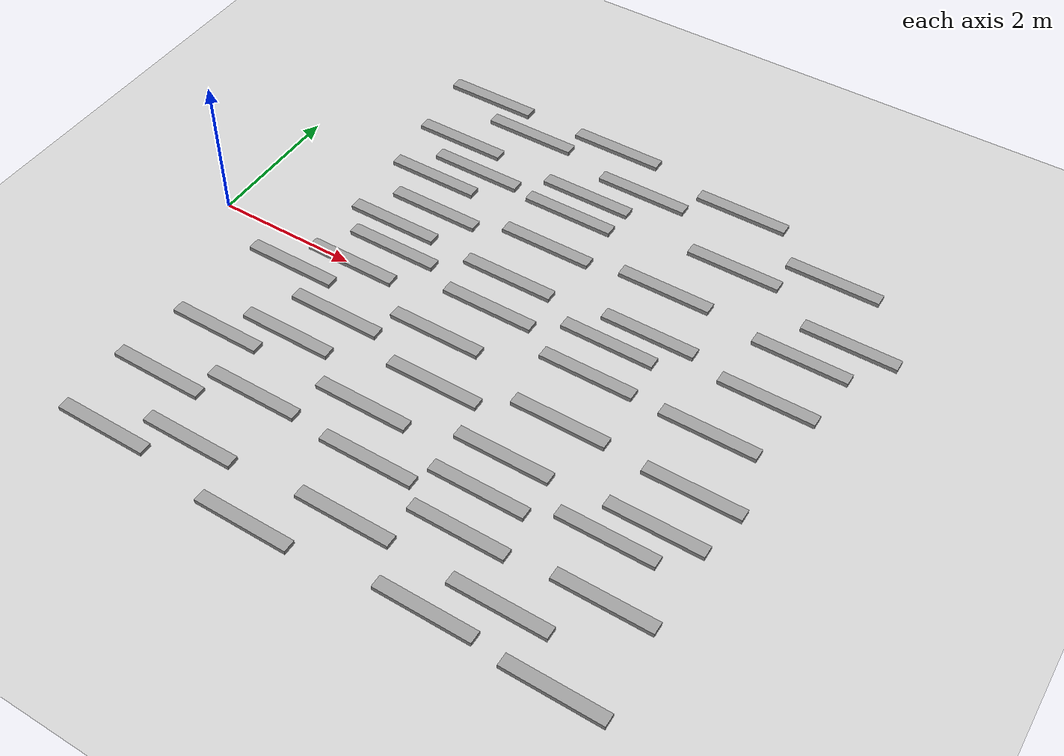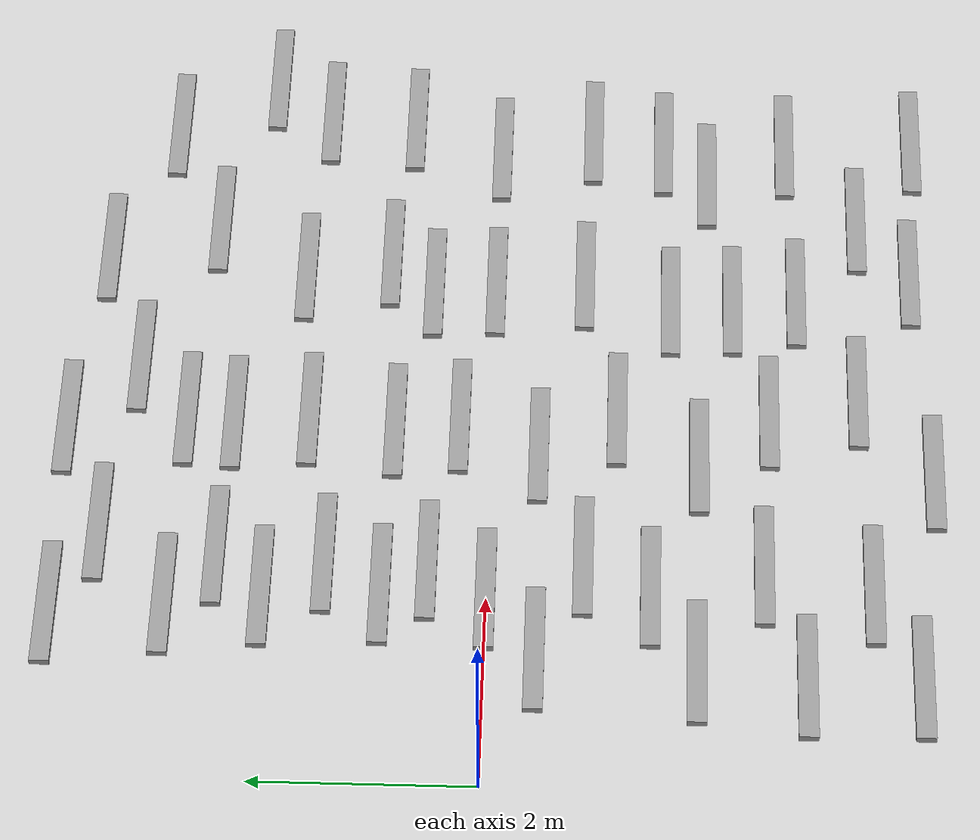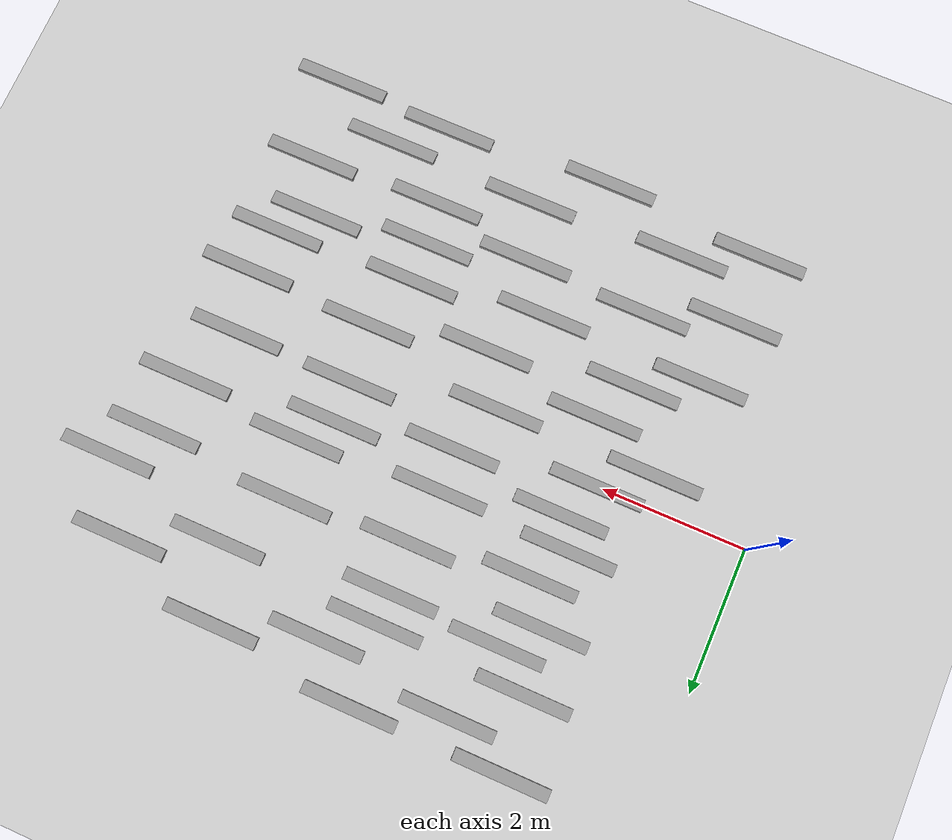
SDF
<sdf version="1.6">
 <world name="default">
  <light name="sun" type="directional">
   <pose>0 0 10 0 -0 0</pose>
   <diffuse>0.8 0.8 0.8 1</diffuse>
   <specular>0.2 0.2 0.2 1</specular>
   <attenuation>
    <range>1000</range>
    <constant>0.9</constant>
    <linear>0.01</linear>
    <quadratic>0.001</quadratic>
   </attenuation>
   <direction>-0.5 0.1 -0.9</direction>
  </light>
  <model name="ground_plane">
   <static>1</static>
   <link name="link">
    <collision name="collision">
     <geometry><plane><normal>0 0 1</normal><size>100 100</size></plane></geometry>
     <surface>
      <contact><ode><kp>1e+12</kp><min_depth>0.01</min_depth></ode></contact>
      <friction><ode><mu>1e+06</mu><mu2>500000</mu2></ode></friction>
     </surface>
    </collision>
    <visual name="visual">
     <cast_shadows>0</cast_shadows>
     <geometry><plane><normal>0 0 1</normal><size>100 100</size></plane></geometry>
     <material>
      <script><uri>file://media/materials/scripts/gazebo.material</uri><name>Gazebo/Grey</name></script>
     </material>
    </visual>
   </link>
  </model>
  <gravity>0 0 -9.8</gravity>
  <magnetic_field>6e-06 2.3e-05 -4.2e-05</magnetic_field>
  <atmosphere type="adiabatic"/>
  <physics name="default_physics" default="0" type="ode">
   <max_step_size>0.001</max_step_size>
   <real_time_factor>1</real_time_factor>
   <real_time_update_rate>0</real_time_update_rate>
  </physics>
  <scene><ambient>0.4 0.4 0.4 1</ambient><background>0.7 0.7 0.7 1</background><shadows>1</shadows></scene>
  <spherical_coordinates>
   <surface_model>EARTH_WGS84</surface_model>
   <latitude_deg>0</latitude_deg>
   <longitude_deg>0</longitude_deg>
   <elevation>0</elevation>
   <heading_deg>0</heading_deg>
  </spherical_coordinates>
  <model name="unit_box_heavy_clone_clone_clone">
   <link name="unit_box::link">
    <inertial>
     <mass>5000</mass>
     <inertia><ixx>833.333</ixx><ixy>0</ixy><ixz>0</ixz><iyy>833.333</iyy><iyz>0</iyz><izz>833.333</izz></inertia>
    </inertial>
    <visual name="visual">
     <geometry><box><size>1.30816 0.176312 0.062582</size></box></geometry>
     <material>
      <script><name>Gazebo/Grey</name><uri>file://media/materials/scripts/gazebo.material</uri></script>
      <shader type="pixel"><normal_map>__default__</normal_map></shader>
     </material>
    </visual>
    <collision name="collision">
     <geometry><box><size>1.30816 0.176312 0.062582</size></box></geometry>
     <surface>
      <friction>
       <ode><mu>1</mu><mu2>1</mu2><fdir1>0 0 0</fdir1><slip1>0</slip1><slip2>0</slip2></ode>
       <torsional>
        <coefficient>1</coefficient>
        <patch_radius>0</patch_radius>
        <surface_radius>0</surface_radius>
        <use_patch_radius>1</use_patch_radius>
        <ode><slip>0</slip></ode>
       </torsional>
      </friction>
      <bounce><restitution_coefficient>0</restitution_coefficient><threshold>1e+06</threshold></bounce>
      <contact>
       <collide_without_contact>0</collide_without_contact>
       <collide_without_contact_bitmask>1</collide_without_contact_bitmask>
       <collide_bitmask>1</collide_bitmask>
       <ode>
        <soft_cfm>0</soft_cfm>
        <soft_erp>0.2</soft_erp>
        <kp>1e+13</kp>
        <kd>1</kd>
        <max_vel>0.01</max_vel>
        <min_depth>0</min_depth>
       </ode>
       <bullet>
        <split_impulse>1</split_impulse>
        <split_impulse_penetration_threshold>-0.01</split_impulse_penetration_threshold>
        <soft_cfm>0</soft_cfm>
        <soft_erp>0.2</soft_erp>
        <kp>1e+13</kp>
        <kd>1</kd>
       </bullet>
      </contact>
     </surface>
    </collision>
   </link>
   <static>0</static>
   <pose>2.08958 0.009134 0.031291 -0 -0 -3e-05</pose>
  </model>
  <model name="unit_box_heavy_clone_clone_clone_clone">
   <link name="unit_box::link">
    <inertial>
     <mass>5000</mass>
     <inertia><ixx>833.333</ixx><ixy>0</ixy><ixz>0</ixz><iyy>833.333</iyy><iyz>0</iyz><izz>833.333</izz></inertia>
    </inertial>
    <visual name="visual">
     <geometry><box><size>1.30816 0.176312 0.062582</size></box></geometry>
     <material>
      <script><name>Gazebo/Grey</name><uri>file://media/materials/scripts/gazebo.material</uri></script>
      <shader type="pixel"><normal_map>__default__</normal_map></shader>
     </material>
    </visual>
    <collision name="collision">
     <geometry><box><size>1.30816 0.176312 0.062582</size></box></geometry>
     <surface>
      <friction>
       <ode><mu>1</mu><mu2>1</mu2><fdir1>0 0 0</fdir1><slip1>0</slip1><slip2>0</slip2></ode>
       <torsional>
        <coefficient>1</coefficient>
        <patch_radius>0</patch_radius>
        <surface_radius>0</surface_radius>
        <use_patch_radius>1</use_patch_radius>
        <ode><slip>0</slip></ode>
       </torsional>
      </friction>
      <bounce><restitution_coefficient>0</restitution_coefficient><threshold>1e+06</threshold></bounce>
      <contact>
       <collide_without_contact>0</collide_without_contact>
       <collide_without_contact_bitmask>1</collide_without_contact_bitmask>
       <collide_bitmask>1</collide_bitmask>
       <ode>
        <soft_cfm>0</soft_cfm>
        <soft_erp>0.2</soft_erp>
        <kp>1e+13</kp>
        <kd>1</kd>
        <max_vel>0.01</max_vel>
        <min_depth>0</min_depth>
       </ode>
       <bullet>
        <split_impulse>1</split_impulse>
        <split_impulse_penetration_threshold>-0.01</split_impulse_penetration_threshold>
        <soft_cfm>0</soft_cfm>
        <soft_erp>0.2</soft_erp>
        <kp>1e+13</kp>
        <kd>1</kd>
       </bullet>
      </contact>
     </surface>
    </collision>
   </link>
   <static>0</static>
   <pose>7.3588 -0.001088 0.031291 0 0 -3e-05</pose>
  </model>
  <model name="unit_box_heavy_clone_clone_clone_clone_0">
   <link name="unit_box::link">
    <inertial>
     <mass>5000</mass>
     <inertia><ixx>833.333</ixx><ixy>0</ixy><ixz>0</ixz><iyy>833.333</iyy><iyz>0</iyz><izz>833.333</izz></inertia>
    </inertial>
    <visual name="visual">
     <geometry><box><size>1.30816 0.176312 0.062582</size></box></geometry>
     <material>
      <script><name>Gazebo/Grey</name><uri>file://media/materials/scripts/gazebo.material</uri></script>
      <shader type="pixel"><normal_map>__default__</normal_map></shader>
     </material>
    </visual>
    <collision name="collision">
     <geometry><box><size>1.30816 0.176312 0.062582</size></box></geometry>
     <surface>
      <friction>
       <ode><mu>1</mu><mu2>1</mu2><fdir1>0 0 0</fdir1><slip1>0</slip1><slip2>0</slip2></ode>
       <torsional>
        <coefficient>1</coefficient>
        <patch_radius>0</patch_radius>
        <surface_radius>0</surface_radius>
        <use_patch_radius>1</use_patch_radius>
        <ode><slip>0</slip></ode>
       </torsional>
      </friction>
      <bounce><restitution_coefficient>0</restitution_coefficient><threshold>1e+06</threshold></bounce>
      <contact>
       <collide_without_contact>0</collide_without_contact>
       <collide_without_contact_bitmask>1</collide_without_contact_bitmask>
       <collide_bitmask>1</collide_bitmask>
       <ode>
        <soft_cfm>0</soft_cfm>
        <soft_erp>0.2</soft_erp>
        <kp>1e+13</kp>
        <kd>1</kd>
        <max_vel>0.01</max_vel>
        <min_depth>0</min_depth>
       </ode>
       <bullet>
        <split_impulse>1</split_impulse>
        <split_impulse_penetration_threshold>-0.01</split_impulse_penetration_threshold>
        <soft_cfm>0</soft_cfm>
        <soft_erp>0.2</soft_erp>
        <kp>1e+13</kp>
        <kd>1</kd>
       </bullet>
      </contact>
     </surface>
    </collision>
   </link>
   <static>0</static>
   <pose>5.67589 0.012274 0.031291 0 0 -2.9e-05</pose>
  </model>
  <model name="unit_box_heavy_clone_clone_clone_clone_1">
   <link name="unit_box::link">
    <inertial>
     <mass>5000</mass>
     <inertia><ixx>833.333</ixx><ixy>0</ixy><ixz>0</ixz><iyy>833.333</iyy><iyz>0</iyz><izz>833.333</izz></inertia>
    </inertial>
    <visual name="visual">
     <geometry><box><size>1.30816 0.176312 0.062582</size></box></geometry>
     <material>
      <script><name>Gazebo/Grey</name><uri>file://media/materials/scripts/gazebo.material</uri></script>
      <shader type="pixel"><normal_map>__default__</normal_map></shader>
     </material>
    </visual>
    <collision name="collision">
     <geometry><box><size>1.30816 0.176312 0.062582</size></box></geometry>
     <surface>
      <friction>
       <ode><mu>1</mu><mu2>1</mu2><fdir1>0 0 0</fdir1><slip1>0</slip1><slip2>0</slip2></ode>
       <torsional>
        <coefficient>1</coefficient>
        <patch_radius>0</patch_radius>
        <surface_radius>0</surface_radius>
        <use_patch_radius>1</use_patch_radius>
        <ode><slip>0</slip></ode>
       </torsional>
      </friction>
      <bounce><restitution_coefficient>0</restitution_coefficient><threshold>1e+06</threshold></bounce>
      <contact>
       <collide_without_contact>0</collide_without_contact>
       <collide_without_contact_bitmask>1</collide_without_contact_bitmask>
       <collide_bitmask>1</collide_bitmask>
       <ode>
        <soft_cfm>0</soft_cfm>
        <soft_erp>0.2</soft_erp>
        <kp>1e+13</kp>
        <kd>1</kd>
        <max_vel>0.01</max_vel>
        <min_depth>0</min_depth>
       </ode>
       <bullet>
        <split_impulse>1</split_impulse>
        <split_impulse_penetration_threshold>-0.01</split_impulse_penetration_threshold>
        <soft_cfm>0</soft_cfm>
        <soft_erp>0.2</soft_erp>
        <kp>1e+13</kp>
        <kd>1</kd>
       </bullet>
      </contact>
     </surface>
    </collision>
   </link>
   <static>0</static>
   <pose>2.38982 0.534391 0.031291 0 0 -3e-05</pose>
  </model>
  <model name="unit_box_heavy_clone_clone_clone_clone_2">
   <link name="unit_box::link">
    <inertial>
     <mass>5000</mass>
     <inertia><ixx>833.333</ixx><ixy>0</ixy><ixz>0</ixz><iyy>833.333</iyy><iyz>0</iyz><izz>833.333</izz></inertia>
    </inertial>
    <visual name="visual">
     <geometry><box><size>1.30816 0.176312 0.062582</size></box></geometry>
     <material>
      <script><name>Gazebo/Grey</name><uri>file://media/materials/scripts/gazebo.material</uri></script>
      <shader type="pixel"><normal_map>__default__</normal_map></shader>
     </material>
    </visual>
    <collision name="collision">
     <geometry><box><size>1.30816 0.176312 0.062582</size></box></geometry>
     <surface>
      <friction>
       <ode><mu>1</mu><mu2>1</mu2><fdir1>0 0 0</fdir1><slip1>0</slip1><slip2>0</slip2></ode>
       <torsional>
        <coefficient>1</coefficient>
        <patch_radius>0</patch_radius>
        <surface_radius>0</surface_radius>
        <use_patch_radius>1</use_patch_radius>
        <ode><slip>0</slip></ode>
       </torsional>
      </friction>
      <bounce><restitution_coefficient>0</restitution_coefficient><threshold>1e+06</threshold></bounce>
      <contact>
       <collide_without_contact>0</collide_without_contact>
       <collide_without_contact_bitmask>1</collide_without_contact_bitmask>
       <collide_bitmask>1</collide_bitmask>
       <ode>
        <soft_cfm>0</soft_cfm>
        <soft_erp>0.2</soft_erp>
        <kp>1e+13</kp>
        <kd>1</kd>
        <max_vel>0.01</max_vel>
        <min_depth>0</min_depth>
       </ode>
       <bullet>
        <split_impulse>1</split_impulse>
        <split_impulse_penetration_threshold>-0.01</split_impulse_penetration_threshold>
        <soft_cfm>0</soft_cfm>
        <soft_erp>0.2</soft_erp>
        <kp>1e+13</kp>
        <kd>1</kd>
       </bullet>
      </contact>
     </surface>
    </collision>
   </link>
   <static>0</static>
   <pose>2.11435 0.94215 0.031291 -0 -0 -3e-05</pose>
  </model>
  <model name="unit_box_heavy_clone_clone_clone_clone_3">
   <link name="unit_box::link">
    <inertial>
     <mass>5000</mass>
     <inertia><ixx>833.333</ixx><ixy>0</ixy><ixz>0</ixz><iyy>833.333</iyy><iyz>0</iyz><izz>833.333</izz></inertia>
    </inertial>
    <visual name="visual">
     <geometry><box><size>1.30816 0.176312 0.062582</size></box></geometry>
     <material>
      <script><name>Gazebo/Grey</name><uri>file://media/materials/scripts/gazebo.material</uri></script>
      <shader type="pixel"><normal_map>__default__</normal_map></shader>
     </material>
    </visual>
    <collision name="collision">
     <geometry><box><size>1.30816 0.176312 0.062582</size></box></geometry>
     <surface>
      <friction>
       <ode><mu>1</mu><mu2>1</mu2><fdir1>0 0 0</fdir1><slip1>0</slip1><slip2>0</slip2></ode>
       <torsional>
        <coefficient>1</coefficient>
        <patch_radius>0</patch_radius>
        <surface_radius>0</surface_radius>
        <use_patch_radius>1</use_patch_radius>
        <ode><slip>0</slip></ode>
       </torsional>
      </friction>
      <bounce><restitution_coefficient>0</restitution_coefficient><threshold>1e+06</threshold></bounce>
      <contact>
       <collide_without_contact>0</collide_without_contact>
       <collide_without_contact_bitmask>1</collide_without_contact_bitmask>
       <collide_bitmask>1</collide_bitmask>
       <ode>
        <soft_cfm>0</soft_cfm>
        <soft_erp>0.2</soft_erp>
        <kp>1e+13</kp>
        <kd>1</kd>
        <max_vel>0.01</max_vel>
        <min_depth>0</min_depth>
       </ode>
       <bullet>
        <split_impulse>1</split_impulse>
        <split_impulse_penetration_threshold>-0.01</split_impulse_penetration_threshold>
        <soft_cfm>0</soft_cfm>
        <soft_erp>0.2</soft_erp>
        <kp>1e+13</kp>
        <kd>1</kd>
       </bullet>
      </contact>
     </surface>
    </collision>
   </link>
   <static>0</static>
   <pose>2.44199 1.45418 0.031291 0 0 -3e-05</pose>
  </model>
  <model name="unit_box_heavy_clone_clone_clone_clone_4">
   <link name="unit_box::link">
    <inertial>
     <mass>5000</mass>
     <inertia><ixx>833.333</ixx><ixy>0</ixy><ixz>0</ixz><iyy>833.333</iyy><iyz>0</iyz><izz>833.333</izz></inertia>
    </inertial>
    <visual name="visual">
     <geometry><box><size>1.30816 0.176312 0.062582</size></box></geometry>
     <material>
      <script><name>Gazebo/Grey</name><uri>file://media/materials/scripts/gazebo.material</uri></script>
      <shader type="pixel"><normal_map>__default__</normal_map></shader>
     </material>
    </visual>
    <collision name="collision">
     <geometry><box><size>1.30816 0.176312 0.062582</size></box></geometry>
     <surface>
      <friction>
       <ode><mu>1</mu><mu2>1</mu2><fdir1>0 0 0</fdir1><slip1>0</slip1><slip2>0</slip2></ode>
       <torsional>
        <coefficient>1</coefficient>
        <patch_radius>0</patch_radius>
        <surface_radius>0</surface_radius>
        <use_patch_radius>1</use_patch_radius>
        <ode><slip>0</slip></ode>
       </torsional>
      </friction>
      <bounce><restitution_coefficient>0</restitution_coefficient><threshold>1e+06</threshold></bounce>
      <contact>
       <collide_without_contact>0</collide_without_contact>
       <collide_without_contact_bitmask>1</collide_without_contact_bitmask>
       <collide_bitmask>1</collide_bitmask>
       <ode>
        <soft_cfm>0</soft_cfm>
        <soft_erp>0.2</soft_erp>
        <kp>1e+13</kp>
        <kd>1</kd>
        <max_vel>0.01</max_vel>
        <min_depth>0</min_depth>
       </ode>
       <bullet>
        <split_impulse>1</split_impulse>
        <split_impulse_penetration_threshold>-0.01</split_impulse_penetration_threshold>
        <soft_cfm>0</soft_cfm>
        <soft_erp>0.2</soft_erp>
        <kp>1e+13</kp>
        <kd>1</kd>
       </bullet>
      </contact>
     </surface>
    </collision>
   </link>
   <static>0</static>
   <pose>2.06355 1.99736 0.031291 -0 -0 -3e-05</pose>
  </model>
  <model name="unit_box_heavy_clone_clone_clone_clone_5">
   <link name="unit_box::link">
    <inertial>
     <mass>5000</mass>
     <inertia><ixx>833.333</ixx><ixy>0</ixy><ixz>0</ixz><iyy>833.333</iyy><iyz>0</iyz><izz>833.333</izz></inertia>
    </inertial>
    <visual name="visual">
     <geometry><box><size>1.30816 0.176312 0.062582</size></box></geometry>
     <material>
      <script><name>Gazebo/Grey</name><uri>file://media/materials/scripts/gazebo.material</uri></script>
      <shader type="pixel"><normal_map>__default__</normal_map></shader>
     </material>
    </visual>
    <collision name="collision">
     <geometry><box><size>1.30816 0.176312 0.062582</size></box></geometry>
     <surface>
      <friction>
       <ode><mu>1</mu><mu2>1</mu2><fdir1>0 0 0</fdir1><slip1>0</slip1><slip2>0</slip2></ode>
       <torsional>
        <coefficient>1</coefficient>
        <patch_radius>0</patch_radius>
        <surface_radius>0</surface_radius>
        <use_patch_radius>1</use_patch_radius>
        <ode><slip>0</slip></ode>
       </torsional>
      </friction>
      <bounce><restitution_coefficient>0</restitution_coefficient><threshold>1e+06</threshold></bounce>
      <contact>
       <collide_without_contact>0</collide_without_contact>
       <collide_without_contact_bitmask>1</collide_without_contact_bitmask>
       <collide_bitmask>1</collide_bitmask>
       <ode>
        <soft_cfm>0</soft_cfm>
        <soft_erp>0.2</soft_erp>
        <kp>1e+13</kp>
        <kd>1</kd>
        <max_vel>0.01</max_vel>
        <min_depth>0</min_depth>
       </ode>
       <bullet>
        <split_impulse>1</split_impulse>
        <split_impulse_penetration_threshold>-0.01</split_impulse_penetration_threshold>
        <soft_cfm>0</soft_cfm>
        <soft_erp>0.2</soft_erp>
        <kp>1e+13</kp>
        <kd>1</kd>
       </bullet>
      </contact>
     </surface>
    </collision>
   </link>
   <static>0</static>
   <pose>2.50068 2.42632 0.031291 0 0 -3e-05</pose>
  </model>
  <model name="unit_box_heavy_clone_clone_clone_clone_6">
   <link name="unit_box::link">
    <inertial>
     <mass>5000</mass>
     <inertia><ixx>833.333</ixx><ixy>0</ixy><ixz>0</ixz><iyy>833.333</iyy><iyz>0</iyz><izz>833.333</izz></inertia>
    </inertial>
    <visual name="visual">
     <geometry><box><size>1.30816 0.176312 0.062582</size></box></geometry>
     <material>
      <script><name>Gazebo/Grey</name><uri>file://media/materials/scripts/gazebo.material</uri></script>
      <shader type="pixel"><normal_map>__default__</normal_map></shader>
     </material>
    </visual>
    <collision name="collision">
     <geometry><box><size>1.30816 0.176312 0.062582</size></box></geometry>
     <surface>
      <friction>
       <ode><mu>1</mu><mu2>1</mu2><fdir1>0 0 0</fdir1><slip1>0</slip1><slip2>0</slip2></ode>
       <torsional>
        <coefficient>1</coefficient>
        <patch_radius>0</patch_radius>
        <surface_radius>0</surface_radius>
        <use_patch_radius>1</use_patch_radius>
        <ode><slip>0</slip></ode>
       </torsional>
      </friction>
      <bounce><restitution_coefficient>0</restitution_coefficient><threshold>1e+06</threshold></bounce>
      <contact>
       <collide_without_contact>0</collide_without_contact>
       <collide_without_contact_bitmask>1</collide_without_contact_bitmask>
       <collide_bitmask>1</collide_bitmask>
       <ode>
        <soft_cfm>0</soft_cfm>
        <soft_erp>0.2</soft_erp>
        <kp>1e+13</kp>
        <kd>1</kd>
        <max_vel>0.01</max_vel>
        <min_depth>0</min_depth>
       </ode>
       <bullet>
        <split_impulse>1</split_impulse>
        <split_impulse_penetration_threshold>-0.01</split_impulse_penetration_threshold>
        <soft_cfm>0</soft_cfm>
        <soft_erp>0.2</soft_erp>
        <kp>1e+13</kp>
        <kd>1</kd>
       </bullet>
      </contact>
     </surface>
    </collision>
   </link>
   <static>0</static>
   <pose>1.95183 2.85478 0.031291 -0 -0 -3e-05</pose>
  </model>
  <model name="unit_box_heavy_clone_clone_clone_clone_7">
   <link name="unit_box::link">
    <inertial>
     <mass>5000</mass>
     <inertia><ixx>833.333</ixx><ixy>0</ixy><ixz>0</ixz><iyy>833.333</iyy><iyz>0</iyz><izz>833.333</izz></inertia>
    </inertial>
    <visual name="visual">
     <geometry><box><size>1.30816 0.176312 0.062582</size></box></geometry>
     <material>
      <script><name>Gazebo/Grey</name><uri>file://media/materials/scripts/gazebo.material</uri></script>
      <shader type="pixel"><normal_map>__default__</normal_map></shader>
     </material>
    </visual>
    <collision name="collision">
     <geometry><box><size>1.30816 0.176312 0.062582</size></box></geometry>
     <surface>
      <friction>
       <ode><mu>1</mu><mu2>1</mu2><fdir1>0 0 0</fdir1><slip1>0</slip1><slip2>0</slip2></ode>
       <torsional>
        <coefficient>1</coefficient>
        <patch_radius>0</patch_radius>
        <surface_radius>0</surface_radius>
        <use_patch_radius>1</use_patch_radius>
        <ode><slip>0</slip></ode>
       </torsional>
      </friction>
      <bounce><restitution_coefficient>0</restitution_coefficient><threshold>1e+06</threshold></bounce>
      <contact>
       <collide_without_contact>0</collide_without_contact>
       <collide_without_contact_bitmask>1</collide_without_contact_bitmask>
       <collide_bitmask>1</collide_bitmask>
       <ode>
        <soft_cfm>0</soft_cfm>
        <soft_erp>0.2</soft_erp>
        <kp>1e+13</kp>
        <kd>1</kd>
        <max_vel>0.01</max_vel>
        <min_depth>0</min_depth>
       </ode>
       <bullet>
        <split_impulse>1</split_impulse>
        <split_impulse_penetration_threshold>-0.01</split_impulse_penetration_threshold>
        <soft_cfm>0</soft_cfm>
        <soft_erp>0.2</soft_erp>
        <kp>1e+13</kp>
        <kd>1</kd>
       </bullet>
      </contact>
     </surface>
    </collision>
   </link>
   <static>0</static>
   <pose>2.73379 3.49196 0.031291 0 0 -3e-05</pose>
  </model>
  <model name="unit_box_heavy_clone_clone_clone_clone_8">
   <link name="unit_box::link">
    <inertial>
     <mass>5000</mass>
     <inertia><ixx>833.333</ixx><ixy>0</ixy><ixz>0</ixz><iyy>833.333</iyy><iyz>0</iyz><izz>833.333</izz></inertia>
    </inertial>
    <visual name="visual">
     <geometry><box><size>1.30816 0.176312 0.062582</size></box></geometry>
     <material>
      <script><name>Gazebo/Grey</name><uri>file://media/materials/scripts/gazebo.material</uri></script>
      <shader type="pixel"><normal_map>__default__</normal_map></shader>
     </material>
    </visual>
    <collision name="collision">
     <geometry><box><size>1.30816 0.176312 0.062582</size></box></geometry>
     <surface>
      <friction>
       <ode><mu>1</mu><mu2>1</mu2><fdir1>0 0 0</fdir1><slip1>0</slip1><slip2>0</slip2></ode>
       <torsional>
        <coefficient>1</coefficient>
        <patch_radius>0</patch_radius>
        <surface_radius>0</surface_radius>
        <use_patch_radius>1</use_patch_radius>
        <ode><slip>0</slip></ode>
       </torsional>
      </friction>
      <bounce><restitution_coefficient>0</restitution_coefficient><threshold>1e+06</threshold></bounce>
      <contact>
       <collide_without_contact>0</collide_without_contact>
       <collide_without_contact_bitmask>1</collide_without_contact_bitmask>
       <collide_bitmask>1</collide_bitmask>
       <ode>
        <soft_cfm>0</soft_cfm>
        <soft_erp>0.2</soft_erp>
        <kp>1e+13</kp>
        <kd>1</kd>
        <max_vel>0.01</max_vel>
        <min_depth>0</min_depth>
       </ode>
       <bullet>
        <split_impulse>1</split_impulse>
        <split_impulse_penetration_threshold>-0.01</split_impulse_penetration_threshold>
        <soft_cfm>0</soft_cfm>
        <soft_erp>0.2</soft_erp>
        <kp>1e+13</kp>
        <kd>1</kd>
       </bullet>
      </contact>
     </surface>
    </collision>
   </link>
   <static>0</static>
   <pose>1.82996 3.87196 0.031291 -0 -0 -3e-05</pose>
  </model>
  <model name="unit_box_heavy_clone_clone_clone_clone_9">
   <link name="unit_box::link">
    <inertial>
     <mass>5000</mass>
     <inertia><ixx>833.333</ixx><ixy>0</ixy><ixz>0</ixz><iyy>833.333</iyy><iyz>0</iyz><izz>833.333</izz></inertia>
    </inertial>
    <visual name="visual">
     <geometry><box><size>1.30816 0.176312 0.062582</size></box></geometry>
     <material>
      <script><name>Gazebo/Grey</name><uri>file://media/materials/scripts/gazebo.material</uri></script>
      <shader type="pixel"><normal_map>__default__</normal_map></shader>
     </material>
    </visual>
    <collision name="collision">
     <geometry><box><size>1.30816 0.176312 0.062582</size></box></geometry>
     <surface>
      <friction>
       <ode><mu>1</mu><mu2>1</mu2><fdir1>0 0 0</fdir1><slip1>0</slip1><slip2>0</slip2></ode>
       <torsional>
        <coefficient>1</coefficient>
        <patch_radius>0</patch_radius>
        <surface_radius>0</surface_radius>
        <use_patch_radius>1</use_patch_radius>
        <ode><slip>0</slip></ode>
       </torsional>
      </friction>
      <bounce><restitution_coefficient>0</restitution_coefficient><threshold>1e+06</threshold></bounce>
      <contact>
       <collide_without_contact>0</collide_without_contact>
       <collide_without_contact_bitmask>1</collide_without_contact_bitmask>
       <collide_bitmask>1</collide_bitmask>
       <ode>
        <soft_cfm>0</soft_cfm>
        <soft_erp>0.2</soft_erp>
        <kp>1e+13</kp>
        <kd>1</kd>
        <max_vel>0.01</max_vel>
        <min_depth>0</min_depth>
       </ode>
       <bullet>
        <split_impulse>1</split_impulse>
        <split_impulse_penetration_threshold>-0.01</split_impulse_penetration_threshold>
        <soft_cfm>0</soft_cfm>
        <soft_erp>0.2</soft_erp>
        <kp>1e+13</kp>
        <kd>1</kd>
       </bullet>
      </contact>
     </surface>
    </collision>
   </link>
   <static>0</static>
   <pose>1.44418 -0.437914 0.031291 0 0 -3e-05</pose>
  </model>
  <model name="unit_box_heavy_clone_clone_clone_clone_10">
   <link name="unit_box::link">
    <inertial>
     <mass>5000</mass>
     <inertia><ixx>833.333</ixx><ixy>0</ixy><ixz>0</ixz><iyy>833.333</iyy><iyz>0</iyz><izz>833.333</izz></inertia>
    </inertial>
    <visual name="visual">
     <geometry><box><size>1.30816 0.176312 0.062582</size></box></geometry>
     <material>
      <script><name>Gazebo/Grey</name><uri>file://media/materials/scripts/gazebo.material</uri></script>
      <shader type="pixel"><normal_map>__default__</normal_map></shader>
     </material>
    </visual>
    <collision name="collision">
     <geometry><box><size>1.30816 0.176312 0.062582</size></box></geometry>
     <surface>
      <friction>
       <ode><mu>1</mu><mu2>1</mu2><fdir1>0 0 0</fdir1><slip1>0</slip1><slip2>0</slip2></ode>
       <torsional>
        <coefficient>1</coefficient>
        <patch_radius>0</patch_radius>
        <surface_radius>0</surface_radius>
        <use_patch_radius>1</use_patch_radius>
        <ode><slip>0</slip></ode>
       </torsional>
      </friction>
      <bounce><restitution_coefficient>0</restitution_coefficient><threshold>1e+06</threshold></bounce>
      <contact>
       <collide_without_contact>0</collide_without_contact>
       <collide_without_contact_bitmask>1</collide_without_contact_bitmask>
       <collide_bitmask>1</collide_bitmask>
       <ode>
        <soft_cfm>0</soft_cfm>
        <soft_erp>0.2</soft_erp>
        <kp>1e+13</kp>
        <kd>1</kd>
        <max_vel>0.01</max_vel>
        <min_depth>0</min_depth>
       </ode>
       <bullet>
        <split_impulse>1</split_impulse>
        <split_impulse_penetration_threshold>-0.01</split_impulse_penetration_threshold>
        <soft_cfm>0</soft_cfm>
        <soft_erp>0.2</soft_erp>
        <kp>1e+13</kp>
        <kd>1</kd>
       </bullet>
      </contact>
     </surface>
    </collision>
   </link>
   <static>0</static>
   <pose>2.46947 -0.850762 0.031291 -0 -0 -3e-05</pose>
  </model>
  <model name="unit_box_heavy_clone_clone_clone_clone_11">
   <link name="unit_box::link">
    <inertial>
     <mass>5000</mass>
     <inertia><ixx>833.333</ixx><ixy>0</ixy><ixz>0</ixz><iyy>833.333</iyy><iyz>0</iyz><izz>833.333</izz></inertia>
    </inertial>
    <visual name="visual">
     <geometry><box><size>1.30816 0.176312 0.062582</size></box></geometry>
     <material>
      <script><name>Gazebo/Grey</name><uri>file://media/materials/scripts/gazebo.material</uri></script>
      <shader type="pixel"><normal_map>__default__</normal_map></shader>
     </material>
    </visual>
    <collision name="collision">
     <geometry><box><size>1.30816 0.176312 0.062582</size></box></geometry>
     <surface>
      <friction>
       <ode><mu>1</mu><mu2>1</mu2><fdir1>0 0 0</fdir1><slip1>0</slip1><slip2>0</slip2></ode>
       <torsional>
        <coefficient>1</coefficient>
        <patch_radius>0</patch_radius>
        <surface_radius>0</surface_radius>
        <use_patch_radius>1</use_patch_radius>
        <ode><slip>0</slip></ode>
       </torsional>
      </friction>
      <bounce><restitution_coefficient>0</restitution_coefficient><threshold>1e+06</threshold></bounce>
      <contact>
       <collide_without_contact>0</collide_without_contact>
       <collide_without_contact_bitmask>1</collide_without_contact_bitmask>
       <collide_bitmask>1</collide_bitmask>
       <ode>
        <soft_cfm>0</soft_cfm>
        <soft_erp>0.2</soft_erp>
        <kp>1e+13</kp>
        <kd>1</kd>
        <max_vel>0.01</max_vel>
        <min_depth>0</min_depth>
       </ode>
       <bullet>
        <split_impulse>1</split_impulse>
        <split_impulse_penetration_threshold>-0.01</split_impulse_penetration_threshold>
        <soft_cfm>0</soft_cfm>
        <soft_erp>0.2</soft_erp>
        <kp>1e+13</kp>
        <kd>1</kd>
       </bullet>
      </contact>
     </surface>
    </collision>
   </link>
   <static>0</static>
   <pose>2.14972 -1.4495 0.031291 0 0 -3e-05</pose>
  </model>
  <model name="unit_box_heavy_clone_clone_clone_clone_12">
   <link name="unit_box::link">
    <inertial>
     <mass>5000</mass>
     <inertia><ixx>833.333</ixx><ixy>0</ixy><ixz>0</ixz><iyy>833.333</iyy><iyz>0</iyz><izz>833.333</izz></inertia>
    </inertial>
    <visual name="visual">
     <geometry><box><size>1.30816 0.176312 0.062582</size></box></geometry>
     <material>
      <script><name>Gazebo/Grey</name><uri>file://media/materials/scripts/gazebo.material</uri></script>
      <shader type="pixel"><normal_map>__default__</normal_map></shader>
     </material>
    </visual>
    <collision name="collision">
     <geometry><box><size>1.30816 0.176312 0.062582</size></box></geometry>
     <surface>
      <friction>
       <ode><mu>1</mu><mu2>1</mu2><fdir1>0 0 0</fdir1><slip1>0</slip1><slip2>0</slip2></ode>
       <torsional>
        <coefficient>1</coefficient>
        <patch_radius>0</patch_radius>
        <surface_radius>0</surface_radius>
        <use_patch_radius>1</use_patch_radius>
        <ode><slip>0</slip></ode>
       </torsional>
      </friction>
      <bounce><restitution_coefficient>0</restitution_coefficient><threshold>1e+06</threshold></bounce>
      <contact>
       <collide_without_contact>0</collide_without_contact>
       <collide_without_contact_bitmask>1</collide_without_contact_bitmask>
       <collide_bitmask>1</collide_bitmask>
       <ode>
        <soft_cfm>0</soft_cfm>
        <soft_erp>0.2</soft_erp>
        <kp>1e+13</kp>
        <kd>1</kd>
        <max_vel>0.01</max_vel>
        <min_depth>0</min_depth>
       </ode>
       <bullet>
        <split_impulse>1</split_impulse>
        <split_impulse_penetration_threshold>-0.01</split_impulse_penetration_threshold>
        <soft_cfm>0</soft_cfm>
        <soft_erp>0.2</soft_erp>
        <kp>1e+13</kp>
        <kd>1</kd>
       </bullet>
      </contact>
     </surface>
    </collision>
   </link>
   <static>0</static>
   <pose>1.34566 -1.85854 0.031291 -0 -0 -3e-05</pose>
  </model>
  <model name="unit_box_heavy_clone_clone_clone_clone_13">
   <link name="unit_box::link">
    <inertial>
     <mass>5000</mass>
     <inertia><ixx>833.333</ixx><ixy>0</ixy><ixz>0</ixz><iyy>833.333</iyy><iyz>0</iyz><izz>833.333</izz></inertia>
    </inertial>
    <visual name="visual">
     <geometry><box><size>1.30816 0.176312 0.062582</size></box></geometry>
     <material>
      <script><name>Gazebo/Grey</name><uri>file://media/materials/scripts/gazebo.material</uri></script>
      <shader type="pixel"><normal_map>__default__</normal_map></shader>
     </material>
    </visual>
    <collision name="collision">
     <geometry><box><size>1.30816 0.176312 0.062582</size></box></geometry>
     <surface>
      <friction>
       <ode><mu>1</mu><mu2>1</mu2><fdir1>0 0 0</fdir1><slip1>0</slip1><slip2>0</slip2></ode>
       <torsional>
        <coefficient>1</coefficient>
        <patch_radius>0</patch_radius>
        <surface_radius>0</surface_radius>
        <use_patch_radius>1</use_patch_radius>
        <ode><slip>0</slip></ode>
       </torsional>
      </friction>
      <bounce><restitution_coefficient>0</restitution_coefficient><threshold>1e+06</threshold></bounce>
      <contact>
       <collide_without_contact>0</collide_without_contact>
       <collide_without_contact_bitmask>1</collide_without_contact_bitmask>
       <collide_bitmask>1</collide_bitmask>
       <ode>
        <soft_cfm>0</soft_cfm>
        <soft_erp>0.2</soft_erp>
        <kp>1e+13</kp>
        <kd>1</kd>
        <max_vel>0.01</max_vel>
        <min_depth>0</min_depth>
       </ode>
       <bullet>
        <split_impulse>1</split_impulse>
        <split_impulse_penetration_threshold>-0.01</split_impulse_penetration_threshold>
        <soft_cfm>0</soft_cfm>
        <soft_erp>0.2</soft_erp>
        <kp>1e+13</kp>
        <kd>1</kd>
       </bullet>
      </contact>
     </surface>
    </collision>
   </link>
   <static>0</static>
   <pose>2.40853 -2.45748 0.031291 0 0 -3e-05</pose>
  </model>
  <model name="unit_box_heavy_clone_clone_clone_clone_14">
   <link name="unit_box::link">
    <inertial>
     <mass>5000</mass>
     <inertia><ixx>833.333</ixx><ixy>0</ixy><ixz>0</ixz><iyy>833.333</iyy><iyz>0</iyz><izz>833.333</izz></inertia>
    </inertial>
    <visual name="visual">
     <geometry><box><size>1.30816 0.176312 0.062582</size></box></geometry>
     <material>
      <script><name>Gazebo/Grey</name><uri>file://media/materials/scripts/gazebo.material</uri></script>
      <shader type="pixel"><normal_map>__default__</normal_map></shader>
     </material>
    </visual>
    <collision name="collision">
     <geometry><box><size>1.30816 0.176312 0.062582</size></box></geometry>
     <surface>
      <friction>
       <ode><mu>1</mu><mu2>1</mu2><fdir1>0 0 0</fdir1><slip1>0</slip1><slip2>0</slip2></ode>
       <torsional>
        <coefficient>1</coefficient>
        <patch_radius>0</patch_radius>
        <surface_radius>0</surface_radius>
        <use_patch_radius>1</use_patch_radius>
        <ode><slip>0</slip></ode>
       </torsional>
      </friction>
      <bounce><restitution_coefficient>0</restitution_coefficient><threshold>1e+06</threshold></bounce>
      <contact>
       <collide_without_contact>0</collide_without_contact>
       <collide_without_contact_bitmask>1</collide_without_contact_bitmask>
       <collide_bitmask>1</collide_bitmask>
       <ode>
        <soft_cfm>0</soft_cfm>
        <soft_erp>0.2</soft_erp>
        <kp>1e+13</kp>
        <kd>1</kd>
        <max_vel>0.01</max_vel>
        <min_depth>0</min_depth>
       </ode>
       <bullet>
        <split_impulse>1</split_impulse>
        <split_impulse_penetration_threshold>-0.01</split_impulse_penetration_threshold>
        <soft_cfm>0</soft_cfm>
        <soft_erp>0.2</soft_erp>
        <kp>1e+13</kp>
        <kd>1</kd>
       </bullet>
      </contact>
     </surface>
    </collision>
   </link>
   <static>0</static>
   <pose>1.21705 -2.82297 0.031291 -0 -0 -3e-05</pose>
  </model>
  <model name="unit_box_heavy_clone_clone_clone_clone_15">
   <link name="unit_box::link">
    <inertial>
     <mass>5000</mass>
     <inertia><ixx>833.333</ixx><ixy>0</ixy><ixz>0</ixz><iyy>833.333</iyy><iyz>0</iyz><izz>833.333</izz></inertia>
    </inertial>
    <visual name="visual">
     <geometry><box><size>1.30816 0.176312 0.062582</size></box></geometry>
     <material>
      <script><name>Gazebo/Grey</name><uri>file://media/materials/scripts/gazebo.material</uri></script>
      <shader type="pixel"><normal_map>__default__</normal_map></shader>
     </material>
    </visual>
    <collision name="collision">
     <geometry><box><size>1.30816 0.176312 0.062582</size></box></geometry>
     <surface>
      <friction>
       <ode><mu>1</mu><mu2>1</mu2><fdir1>0 0 0</fdir1><slip1>0</slip1><slip2>0</slip2></ode>
       <torsional>
        <coefficient>1</coefficient>
        <patch_radius>0</patch_radius>
        <surface_radius>0</surface_radius>
        <use_patch_radius>1</use_patch_radius>
        <ode><slip>0</slip></ode>
       </torsional>
      </friction>
      <bounce><restitution_coefficient>0</restitution_coefficient><threshold>1e+06</threshold></bounce>
      <contact>
       <collide_without_contact>0</collide_without_contact>
       <collide_without_contact_bitmask>1</collide_without_contact_bitmask>
       <collide_bitmask>1</collide_bitmask>
       <ode>
        <soft_cfm>0</soft_cfm>
        <soft_erp>0.2</soft_erp>
        <kp>1e+13</kp>
        <kd>1</kd>
        <max_vel>0.01</max_vel>
        <min_depth>0</min_depth>
       </ode>
       <bullet>
        <split_impulse>1</split_impulse>
        <split_impulse_penetration_threshold>-0.01</split_impulse_penetration_threshold>
        <soft_cfm>0</soft_cfm>
        <soft_erp>0.2</soft_erp>
        <kp>1e+13</kp>
        <kd>1</kd>
       </bullet>
      </contact>
     </surface>
    </collision>
   </link>
   <static>0</static>
   <pose>2.22318 -3.42702 0.031291 0 0 -3e-05</pose>
  </model>
  <model name="unit_box_heavy_clone_clone_clone_clone_16">
   <link name="unit_box::link">
    <inertial>
     <mass>5000</mass>
     <inertia><ixx>833.333</ixx><ixy>0</ixy><ixz>0</ixz><iyy>833.333</iyy><iyz>0</iyz><izz>833.333</izz></inertia>
    </inertial>
    <visual name="visual">
     <geometry><box><size>1.30816 0.176312 0.062582</size></box></geometry>
     <material>
      <script><name>Gazebo/Grey</name><uri>file://media/materials/scripts/gazebo.material</uri></script>
      <shader type="pixel"><normal_map>__default__</normal_map></shader>
     </material>
    </visual>
    <collision name="collision">
     <geometry><box><size>1.30816 0.176312 0.062582</size></box></geometry>
     <surface>
      <friction>
       <ode><mu>1</mu><mu2>1</mu2><fdir1>0 0 0</fdir1><slip1>0</slip1><slip2>0</slip2></ode>
       <torsional>
        <coefficient>1</coefficient>
        <patch_radius>0</patch_radius>
        <surface_radius>0</surface_radius>
        <use_patch_radius>1</use_patch_radius>
        <ode><slip>0</slip></ode>
       </torsional>
      </friction>
      <bounce><restitution_coefficient>0</restitution_coefficient><threshold>1e+06</threshold></bounce>
      <contact>
       <collide_without_contact>0</collide_without_contact>
       <collide_without_contact_bitmask>1</collide_without_contact_bitmask>
       <collide_bitmask>1</collide_bitmask>
       <ode>
        <soft_cfm>0</soft_cfm>
        <soft_erp>0.2</soft_erp>
        <kp>1e+13</kp>
        <kd>1</kd>
        <max_vel>0.01</max_vel>
        <min_depth>0</min_depth>
       </ode>
       <bullet>
        <split_impulse>1</split_impulse>
        <split_impulse_penetration_threshold>-0.01</split_impulse_penetration_threshold>
        <soft_cfm>0</soft_cfm>
        <soft_erp>0.2</soft_erp>
        <kp>1e+13</kp>
        <kd>1</kd>
       </bullet>
      </contact>
     </surface>
    </collision>
   </link>
   <static>0</static>
   <pose>1.23338 -3.83282 0.031291 -0 -0 -3e-05</pose>
  </model>
  <model name="unit_box_heavy_clone_clone_clone_clone_17">
   <link name="unit_box::link">
    <inertial>
     <mass>5000</mass>
     <inertia><ixx>833.333</ixx><ixy>0</ixy><ixz>0</ixz><iyy>833.333</iyy><iyz>0</iyz><izz>833.333</izz></inertia>
    </inertial>
    <visual name="visual">
     <geometry><box><size>1.30816 0.176312 0.062582</size></box></geometry>
     <material>
      <script><name>Gazebo/Grey</name><uri>file://media/materials/scripts/gazebo.material</uri></script>
      <shader type="pixel"><normal_map>__default__</normal_map></shader>
     </material>
    </visual>
    <collision name="collision">
     <geometry><box><size>1.30816 0.176312 0.062582</size></box></geometry>
     <surface>
      <friction>
       <ode><mu>1</mu><mu2>1</mu2><fdir1>0 0 0</fdir1><slip1>0</slip1><slip2>0</slip2></ode>
       <torsional>
        <coefficient>1</coefficient>
        <patch_radius>0</patch_radius>
        <surface_radius>0</surface_radius>
        <use_patch_radius>1</use_patch_radius>
        <ode><slip>0</slip></ode>
       </torsional>
      </friction>
      <bounce><restitution_coefficient>0</restitution_coefficient><threshold>1e+06</threshold></bounce>
      <contact>
       <collide_without_contact>0</collide_without_contact>
       <collide_without_contact_bitmask>1</collide_without_contact_bitmask>
       <collide_bitmask>1</collide_bitmask>
       <ode>
        <soft_cfm>0</soft_cfm>
        <soft_erp>0.2</soft_erp>
        <kp>1e+13</kp>
        <kd>1</kd>
        <max_vel>0.01</max_vel>
        <min_depth>0</min_depth>
       </ode>
       <bullet>
        <split_impulse>1</split_impulse>
        <split_impulse_penetration_threshold>-0.01</split_impulse_penetration_threshold>
        <soft_cfm>0</soft_cfm>
        <soft_erp>0.2</soft_erp>
        <kp>1e+13</kp>
        <kd>1</kd>
       </bullet>
      </contact>
     </surface>
    </collision>
   </link>
   <static>0</static>
   <pose>3.633 -1.88112 0.031291 0 0 -3e-05</pose>
  </model>
  <model name="unit_box_heavy_clone_clone_clone_clone_18">
   <link name="unit_box::link">
    <inertial>
     <mass>5000</mass>
     <inertia><ixx>833.333</ixx><ixy>0</ixy><ixz>0</ixz><iyy>833.333</iyy><iyz>0</iyz><izz>833.333</izz></inertia>
    </inertial>
    <visual name="visual">
     <geometry><box><size>1.30816 0.176312 0.062582</size></box></geometry>
     <material>
      <script><name>Gazebo/Grey</name><uri>file://media/materials/scripts/gazebo.material</uri></script>
      <shader type="pixel"><normal_map>__default__</normal_map></shader>
     </material>
    </visual>
    <collision name="collision">
     <geometry><box><size>1.30816 0.176312 0.062582</size></box></geometry>
     <surface>
      <friction>
       <ode><mu>1</mu><mu2>1</mu2><fdir1>0 0 0</fdir1><slip1>0</slip1><slip2>0</slip2></ode>
       <torsional>
        <coefficient>1</coefficient>
        <patch_radius>0</patch_radius>
        <surface_radius>0</surface_radius>
        <use_patch_radius>1</use_patch_radius>
        <ode><slip>0</slip></ode>
       </torsional>
      </friction>
      <bounce><restitution_coefficient>0</restitution_coefficient><threshold>1e+06</threshold></bounce>
      <contact>
       <collide_without_contact>0</collide_without_contact>
       <collide_without_contact_bitmask>1</collide_without_contact_bitmask>
       <collide_bitmask>1</collide_bitmask>
       <ode>
        <soft_cfm>0</soft_cfm>
        <soft_erp>0.2</soft_erp>
        <kp>1e+13</kp>
        <kd>1</kd>
        <max_vel>0.01</max_vel>
        <min_depth>0</min_depth>
       </ode>
       <bullet>
        <split_impulse>1</split_impulse>
        <split_impulse_penetration_threshold>-0.01</split_impulse_penetration_threshold>
        <soft_cfm>0</soft_cfm>
        <soft_erp>0.2</soft_erp>
        <kp>1e+13</kp>
        <kd>1</kd>
       </bullet>
      </contact>
     </surface>
    </collision>
   </link>
   <static>0</static>
   <pose>4.16259 -1.13321 0.031291 -0 -0 -3e-05</pose>
  </model>
  <model name="unit_box_heavy_clone_clone_clone_clone_19">
   <link name="unit_box::link">
    <inertial>
     <mass>5000</mass>
     <inertia><ixx>833.333</ixx><ixy>0</ixy><ixz>0</ixz><iyy>833.333</iyy><iyz>0</iyz><izz>833.333</izz></inertia>
    </inertial>
    <visual name="visual">
     <geometry><box><size>1.30816 0.176312 0.062582</size></box></geometry>
     <material>
      <script><name>Gazebo/Grey</name><uri>file://media/materials/scripts/gazebo.material</uri></script>
      <shader type="pixel"><normal_map>__default__</normal_map></shader>
     </material>
    </visual>
    <collision name="collision">
     <geometry><box><size>1.30816 0.176312 0.062582</size></box></geometry>
     <surface>
      <friction>
       <ode><mu>1</mu><mu2>1</mu2><fdir1>0 0 0</fdir1><slip1>0</slip1><slip2>0</slip2></ode>
       <torsional>
        <coefficient>1</coefficient>
        <patch_radius>0</patch_radius>
        <surface_radius>0</surface_radius>
        <use_patch_radius>1</use_patch_radius>
        <ode><slip>0</slip></ode>
       </torsional>
      </friction>
      <bounce><restitution_coefficient>0</restitution_coefficient><threshold>1e+06</threshold></bounce>
      <contact>
       <collide_without_contact>0</collide_without_contact>
       <collide_without_contact_bitmask>1</collide_without_contact_bitmask>
       <collide_bitmask>1</collide_bitmask>
       <ode>
        <soft_cfm>0</soft_cfm>
        <soft_erp>0.2</soft_erp>
        <kp>1e+13</kp>
        <kd>1</kd>
        <max_vel>0.01</max_vel>
        <min_depth>0</min_depth>
       </ode>
       <bullet>
        <split_impulse>1</split_impulse>
        <split_impulse_penetration_threshold>-0.01</split_impulse_penetration_threshold>
        <soft_cfm>0</soft_cfm>
        <soft_erp>0.2</soft_erp>
        <kp>1e+13</kp>
        <kd>1</kd>
       </bullet>
      </contact>
     </surface>
    </collision>
   </link>
   <static>0</static>
   <pose>3.72327 -0.428406 0.031291 0 0 -3e-05</pose>
  </model>
  <model name="unit_box_heavy_clone_clone_clone_clone_20">
   <link name="unit_box::link">
    <inertial>
     <mass>5000</mass>
     <inertia><ixx>833.333</ixx><ixy>0</ixy><ixz>0</ixz><iyy>833.333</iyy><iyz>0</iyz><izz>833.333</izz></inertia>
    </inertial>
    <visual name="visual">
     <geometry><box><size>1.30816 0.176312 0.062582</size></box></geometry>
     <material>
      <script><name>Gazebo/Grey</name><uri>file://media/materials/scripts/gazebo.material</uri></script>
      <shader type="pixel"><normal_map>__default__</normal_map></shader>
     </material>
    </visual>
    <collision name="collision">
     <geometry><box><size>1.30816 0.176312 0.062582</size></box></geometry>
     <surface>
      <friction>
       <ode><mu>1</mu><mu2>1</mu2><fdir1>0 0 0</fdir1><slip1>0</slip1><slip2>0</slip2></ode>
       <torsional>
        <coefficient>1</coefficient>
        <patch_radius>0</patch_radius>
        <surface_radius>0</surface_radius>
        <use_patch_radius>1</use_patch_radius>
        <ode><slip>0</slip></ode>
       </torsional>
      </friction>
      <bounce><restitution_coefficient>0</restitution_coefficient><threshold>1e+06</threshold></bounce>
      <contact>
       <collide_without_contact>0</collide_without_contact>
       <collide_without_contact_bitmask>1</collide_without_contact_bitmask>
       <collide_bitmask>1</collide_bitmask>
       <ode>
        <soft_cfm>0</soft_cfm>
        <soft_erp>0.2</soft_erp>
        <kp>1e+13</kp>
        <kd>1</kd>
        <max_vel>0.01</max_vel>
        <min_depth>0</min_depth>
       </ode>
       <bullet>
        <split_impulse>1</split_impulse>
        <split_impulse_penetration_threshold>-0.01</split_impulse_penetration_threshold>
        <soft_cfm>0</soft_cfm>
        <soft_erp>0.2</soft_erp>
        <kp>1e+13</kp>
        <kd>1</kd>
       </bullet>
      </contact>
     </surface>
    </collision>
   </link>
   <static>0</static>
   <pose>4.04561 0.297955 0.031291 -0 -0 -3e-05</pose>
  </model>
  <model name="unit_box_heavy_clone_clone_clone_clone_21">
   <link name="unit_box::link">
    <inertial>
     <mass>5000</mass>
     <inertia><ixx>833.333</ixx><ixy>0</ixy><ixz>0</ixz><iyy>833.333</iyy><iyz>0</iyz><izz>833.333</izz></inertia>
    </inertial>
    <visual name="visual">
     <geometry><box><size>1.30816 0.176312 0.062582</size></box></geometry>
     <material>
      <script><name>Gazebo/Grey</name><uri>file://media/materials/scripts/gazebo.material</uri></script>
      <shader type="pixel"><normal_map>__default__</normal_map></shader>
     </material>
    </visual>
    <collision name="collision">
     <geometry><box><size>1.30816 0.176312 0.062582</size></box></geometry>
     <surface>
      <friction>
       <ode><mu>1</mu><mu2>1</mu2><fdir1>0 0 0</fdir1><slip1>0</slip1><slip2>0</slip2></ode>
       <torsional>
        <coefficient>1</coefficient>
        <patch_radius>0</patch_radius>
        <surface_radius>0</surface_radius>
        <use_patch_radius>1</use_patch_radius>
        <ode><slip>0</slip></ode>
       </torsional>
      </friction>
      <bounce><restitution_coefficient>0</restitution_coefficient><threshold>1e+06</threshold></bounce>
      <contact>
       <collide_without_contact>0</collide_without_contact>
       <collide_without_contact_bitmask>1</collide_without_contact_bitmask>
       <collide_bitmask>1</collide_bitmask>
       <ode>
        <soft_cfm>0</soft_cfm>
        <soft_erp>0.2</soft_erp>
        <kp>1e+13</kp>
        <kd>1</kd>
        <max_vel>0.01</max_vel>
        <min_depth>0</min_depth>
       </ode>
       <bullet>
        <split_impulse>1</split_impulse>
        <split_impulse_penetration_threshold>-0.01</split_impulse_penetration_threshold>
        <soft_cfm>0</soft_cfm>
        <soft_erp>0.2</soft_erp>
        <kp>1e+13</kp>
        <kd>1</kd>
       </bullet>
      </contact>
     </surface>
    </collision>
   </link>
   <static>0</static>
   <pose>3.9751 0.887963 0.031291 0 0 -3e-05</pose>
  </model>
  <model name="unit_box_heavy_clone_clone_clone_clone_22">
   <link name="unit_box::link">
    <inertial>
     <mass>5000</mass>
     <inertia><ixx>833.333</ixx><ixy>0</ixy><ixz>0</ixz><iyy>833.333</iyy><iyz>0</iyz><izz>833.333</izz></inertia>
    </inertial>
    <visual name="visual">
     <geometry><box><size>1.30816 0.176312 0.062582</size></box></geometry>
     <material>
      <script><name>Gazebo/Grey</name><uri>file://media/materials/scripts/gazebo.material</uri></script>
      <shader type="pixel"><normal_map>__default__</normal_map></shader>
     </material>
    </visual>
    <collision name="collision">
     <geometry><box><size>1.30816 0.176312 0.062582</size></box></geometry>
     <surface>
      <friction>
       <ode><mu>1</mu><mu2>1</mu2><fdir1>0 0 0</fdir1><slip1>0</slip1><slip2>0</slip2></ode>
       <torsional>
        <coefficient>1</coefficient>
        <patch_radius>0</patch_radius>
        <surface_radius>0</surface_radius>
        <use_patch_radius>1</use_patch_radius>
        <ode><slip>0</slip></ode>
       </torsional>
      </friction>
      <bounce><restitution_coefficient>0</restitution_coefficient><threshold>1e+06</threshold></bounce>
      <contact>
       <collide_without_contact>0</collide_without_contact>
       <collide_without_contact_bitmask>1</collide_without_contact_bitmask>
       <collide_bitmask>1</collide_bitmask>
       <ode>
        <soft_cfm>0</soft_cfm>
        <soft_erp>0.2</soft_erp>
        <kp>1e+13</kp>
        <kd>1</kd>
        <max_vel>0.01</max_vel>
        <min_depth>0</min_depth>
       </ode>
       <bullet>
        <split_impulse>1</split_impulse>
        <split_impulse_penetration_threshold>-0.01</split_impulse_penetration_threshold>
        <soft_cfm>0</soft_cfm>
        <soft_erp>0.2</soft_erp>
        <kp>1e+13</kp>
        <kd>1</kd>
       </bullet>
      </contact>
     </surface>
    </collision>
   </link>
   <static>0</static>
   <pose>4.08567 1.67192 0.031291 -0 -0 -3e-05</pose>
  </model>
  <model name="unit_box_heavy_clone_clone_clone_clone_23">
   <link name="unit_box::link">
    <inertial>
     <mass>5000</mass>
     <inertia><ixx>833.333</ixx><ixy>0</ixy><ixz>0</ixz><iyy>833.333</iyy><iyz>0</iyz><izz>833.333</izz></inertia>
    </inertial>
    <visual name="visual">
     <geometry><box><size>1.30816 0.176312 0.062582</size></box></geometry>
     <material>
      <script><name>Gazebo/Grey</name><uri>file://media/materials/scripts/gazebo.material</uri></script>
      <shader type="pixel"><normal_map>__default__</normal_map></shader>
     </material>
    </visual>
    <collision name="collision">
     <geometry><box><size>1.30816 0.176312 0.062582</size></box></geometry>
     <surface>
      <friction>
       <ode><mu>1</mu><mu2>1</mu2><fdir1>0 0 0</fdir1><slip1>0</slip1><slip2>0</slip2></ode>
       <torsional>
        <coefficient>1</coefficient>
        <patch_radius>0</patch_radius>
        <surface_radius>0</surface_radius>
        <use_patch_radius>1</use_patch_radius>
        <ode><slip>0</slip></ode>
       </torsional>
      </friction>
      <bounce><restitution_coefficient>0</restitution_coefficient><threshold>1e+06</threshold></bounce>
      <contact>
       <collide_without_contact>0</collide_without_contact>
       <collide_without_contact_bitmask>1</collide_without_contact_bitmask>
       <collide_bitmask>1</collide_bitmask>
       <ode>
        <soft_cfm>0</soft_cfm>
        <soft_erp>0.2</soft_erp>
        <kp>1e+13</kp>
        <kd>1</kd>
        <max_vel>0.01</max_vel>
        <min_depth>0</min_depth>
       </ode>
       <bullet>
        <split_impulse>1</split_impulse>
        <split_impulse_penetration_threshold>-0.01</split_impulse_penetration_threshold>
        <soft_cfm>0</soft_cfm>
        <soft_erp>0.2</soft_erp>
        <kp>1e+13</kp>
        <kd>1</kd>
       </bullet>
      </contact>
     </surface>
    </collision>
   </link>
   <static>0</static>
   <pose>4.02745 2.36033 0.031291 0 0 -3e-05</pose>
  </model>
  <model name="unit_box_heavy_clone_clone_clone_clone_24">
   <link name="unit_box::link">
    <inertial>
     <mass>5000</mass>
     <inertia><ixx>833.333</ixx><ixy>0</ixy><ixz>0</ixz><iyy>833.333</iyy><iyz>0</iyz><izz>833.333</izz></inertia>
    </inertial>
    <visual name="visual">
     <geometry><box><size>1.30816 0.176312 0.062582</size></box></geometry>
     <material>
      <script><name>Gazebo/Grey</name><uri>file://media/materials/scripts/gazebo.material</uri></script>
      <shader type="pixel"><normal_map>__default__</normal_map></shader>
     </material>
    </visual>
    <collision name="collision">
     <geometry><box><size>1.30816 0.176312 0.062582</size></box></geometry>
     <surface>
      <friction>
       <ode><mu>1</mu><mu2>1</mu2><fdir1>0 0 0</fdir1><slip1>0</slip1><slip2>0</slip2></ode>
       <torsional>
        <coefficient>1</coefficient>
        <patch_radius>0</patch_radius>
        <surface_radius>0</surface_radius>
        <use_patch_radius>1</use_patch_radius>
        <ode><slip>0</slip></ode>
       </torsional>
      </friction>
      <bounce><restitution_coefficient>0</restitution_coefficient><threshold>1e+06</threshold></bounce>
      <contact>
       <collide_without_contact>0</collide_without_contact>
       <collide_without_contact_bitmask>1</collide_without_contact_bitmask>
       <collide_bitmask>1</collide_bitmask>
       <ode>
        <soft_cfm>0</soft_cfm>
        <soft_erp>0.2</soft_erp>
        <kp>1e+13</kp>
        <kd>1</kd>
        <max_vel>0.01</max_vel>
        <min_depth>0</min_depth>
       </ode>
       <bullet>
        <split_impulse>1</split_impulse>
        <split_impulse_penetration_threshold>-0.01</split_impulse_penetration_threshold>
        <soft_cfm>0</soft_cfm>
        <soft_erp>0.2</soft_erp>
        <kp>1e+13</kp>
        <kd>1</kd>
       </bullet>
      </contact>
     </surface>
    </collision>
   </link>
   <static>0</static>
   <pose>4.05825 2.79068 0.031291 -0 -0 -3e-05</pose>
  </model>
  <model name="unit_box_heavy_clone_clone_clone_clone_25">
   <link name="unit_box::link">
    <inertial>
     <mass>5000</mass>
     <inertia><ixx>833.333</ixx><ixy>0</ixy><ixz>0</ixz><iyy>833.333</iyy><iyz>0</iyz><izz>833.333</izz></inertia>
    </inertial>
    <visual name="visual">
     <geometry><box><size>1.30816 0.176312 0.062582</size></box></geometry>
     <material>
      <script><name>Gazebo/Grey</name><uri>file://media/materials/scripts/gazebo.material</uri></script>
      <shader type="pixel"><normal_map>__default__</normal_map></shader>
     </material>
    </visual>
    <collision name="collision">
     <geometry><box><size>1.30816 0.176312 0.062582</size></box></geometry>
     <surface>
      <friction>
       <ode><mu>1</mu><mu2>1</mu2><fdir1>0 0 0</fdir1><slip1>0</slip1><slip2>0</slip2></ode>
       <torsional>
        <coefficient>1</coefficient>
        <patch_radius>0</patch_radius>
        <surface_radius>0</surface_radius>
        <use_patch_radius>1</use_patch_radius>
        <ode><slip>0</slip></ode>
       </torsional>
      </friction>
      <bounce><restitution_coefficient>0</restitution_coefficient><threshold>1e+06</threshold></bounce>
      <contact>
       <collide_without_contact>0</collide_without_contact>
       <collide_without_contact_bitmask>1</collide_without_contact_bitmask>
       <collide_bitmask>1</collide_bitmask>
       <ode>
        <soft_cfm>0</soft_cfm>
        <soft_erp>0.2</soft_erp>
        <kp>1e+13</kp>
        <kd>1</kd>
        <max_vel>0.01</max_vel>
        <min_depth>0</min_depth>
       </ode>
       <bullet>
        <split_impulse>1</split_impulse>
        <split_impulse_penetration_threshold>-0.01</split_impulse_penetration_threshold>
        <soft_cfm>0</soft_cfm>
        <soft_erp>0.2</soft_erp>
        <kp>1e+13</kp>
        <kd>1</kd>
       </bullet>
      </contact>
     </surface>
    </collision>
   </link>
   <static>0</static>
   <pose>4.67342 3.25892 0.031291 0 0 -3e-05</pose>
  </model>
  <model name="unit_box_heavy_clone_clone_clone_clone_26">
   <link name="unit_box::link">
    <inertial>
     <mass>5000</mass>
     <inertia><ixx>833.333</ixx><ixy>0</ixy><ixz>0</ixz><iyy>833.333</iyy><iyz>0</iyz><izz>833.333</izz></inertia>
    </inertial>
    <visual name="visual">
     <geometry><box><size>1.30816 0.176312 0.062582</size></box></geometry>
     <material>
      <script><name>Gazebo/Grey</name><uri>file://media/materials/scripts/gazebo.material</uri></script>
      <shader type="pixel"><normal_map>__default__</normal_map></shader>
     </material>
    </visual>
    <collision name="collision">
     <geometry><box><size>1.30816 0.176312 0.062582</size></box></geometry>
     <surface>
      <friction>
       <ode><mu>1</mu><mu2>1</mu2><fdir1>0 0 0</fdir1><slip1>0</slip1><slip2>0</slip2></ode>
       <torsional>
        <coefficient>1</coefficient>
        <patch_radius>0</patch_radius>
        <surface_radius>0</surface_radius>
        <use_patch_radius>1</use_patch_radius>
        <ode><slip>0</slip></ode>
       </torsional>
      </friction>
      <bounce><restitution_coefficient>0</restitution_coefficient><threshold>1e+06</threshold></bounce>
      <contact>
       <collide_without_contact>0</collide_without_contact>
       <collide_without_contact_bitmask>1</collide_without_contact_bitmask>
       <collide_bitmask>1</collide_bitmask>
       <ode>
        <soft_cfm>0</soft_cfm>
        <soft_erp>0.2</soft_erp>
        <kp>1e+13</kp>
        <kd>1</kd>
        <max_vel>0.01</max_vel>
        <min_depth>0</min_depth>
       </ode>
       <bullet>
        <split_impulse>1</split_impulse>
        <split_impulse_penetration_threshold>-0.01</split_impulse_penetration_threshold>
        <soft_cfm>0</soft_cfm>
        <soft_erp>0.2</soft_erp>
        <kp>1e+13</kp>
        <kd>1</kd>
       </bullet>
      </contact>
     </surface>
    </collision>
   </link>
   <static>0</static>
   <pose>3.93155 3.877 0.031291 -0 -0 -3e-05</pose>
  </model>
  <model name="unit_box_heavy_clone_clone_clone_clone_27">
   <link name="unit_box::link">
    <inertial>
     <mass>5000</mass>
     <inertia><ixx>833.333</ixx><ixy>0</ixy><ixz>0</ixz><iyy>833.333</iyy><iyz>0</iyz><izz>833.333</izz></inertia>
    </inertial>
    <visual name="visual">
     <geometry><box><size>1.30816 0.176312 0.062582</size></box></geometry>
     <material>
      <script><name>Gazebo/Grey</name><uri>file://media/materials/scripts/gazebo.material</uri></script>
      <shader type="pixel"><normal_map>__default__</normal_map></shader>
     </material>
    </visual>
    <collision name="collision">
     <geometry><box><size>1.30816 0.176312 0.062582</size></box></geometry>
     <surface>
      <friction>
       <ode><mu>1</mu><mu2>1</mu2><fdir1>0 0 0</fdir1><slip1>0</slip1><slip2>0</slip2></ode>
       <torsional>
        <coefficient>1</coefficient>
        <patch_radius>0</patch_radius>
        <surface_radius>0</surface_radius>
        <use_patch_radius>1</use_patch_radius>
        <ode><slip>0</slip></ode>
       </torsional>
      </friction>
      <bounce><restitution_coefficient>0</restitution_coefficient><threshold>1e+06</threshold></bounce>
      <contact>
       <collide_without_contact>0</collide_without_contact>
       <collide_without_contact_bitmask>1</collide_without_contact_bitmask>
       <collide_bitmask>1</collide_bitmask>
       <ode>
        <soft_cfm>0</soft_cfm>
        <soft_erp>0.2</soft_erp>
        <kp>1e+13</kp>
        <kd>1</kd>
        <max_vel>0.01</max_vel>
        <min_depth>0</min_depth>
       </ode>
       <bullet>
        <split_impulse>1</split_impulse>
        <split_impulse_penetration_threshold>-0.01</split_impulse_penetration_threshold>
        <soft_cfm>0</soft_cfm>
        <soft_erp>0.2</soft_erp>
        <kp>1e+13</kp>
        <kd>1</kd>
       </bullet>
      </contact>
     </surface>
    </collision>
   </link>
   <static>0</static>
   <pose>4.16552 -2.51812 0.031291 0 0 -3e-05</pose>
  </model>
  <model name="unit_box_heavy_clone_clone_clone_clone_28">
   <link name="unit_box::link">
    <inertial>
     <mass>5000</mass>
     <inertia><ixx>833.333</ixx><ixy>0</ixy><ixz>0</ixz><iyy>833.333</iyy><iyz>0</iyz><izz>833.333</izz></inertia>
    </inertial>
    <visual name="visual">
     <geometry><box><size>1.30816 0.176312 0.062582</size></box></geometry>
     <material>
      <script><name>Gazebo/Grey</name><uri>file://media/materials/scripts/gazebo.material</uri></script>
      <shader type="pixel"><normal_map>__default__</normal_map></shader>
     </material>
    </visual>
    <collision name="collision">
     <geometry><box><size>1.30816 0.176312 0.062582</size></box></geometry>
     <surface>
      <friction>
       <ode><mu>1</mu><mu2>1</mu2><fdir1>0 0 0</fdir1><slip1>0</slip1><slip2>0</slip2></ode>
       <torsional>
        <coefficient>1</coefficient>
        <patch_radius>0</patch_radius>
        <surface_radius>0</surface_radius>
        <use_patch_radius>1</use_patch_radius>
        <ode><slip>0</slip></ode>
       </torsional>
      </friction>
      <bounce><restitution_coefficient>0</restitution_coefficient><threshold>1e+06</threshold></bounce>
      <contact>
       <collide_without_contact>0</collide_without_contact>
       <collide_without_contact_bitmask>1</collide_without_contact_bitmask>
       <collide_bitmask>1</collide_bitmask>
       <ode>
        <soft_cfm>0</soft_cfm>
        <soft_erp>0.2</soft_erp>
        <kp>1e+13</kp>
        <kd>1</kd>
        <max_vel>0.01</max_vel>
        <min_depth>0</min_depth>
       </ode>
       <bullet>
        <split_impulse>1</split_impulse>
        <split_impulse_penetration_threshold>-0.01</split_impulse_penetration_threshold>
        <soft_cfm>0</soft_cfm>
        <soft_erp>0.2</soft_erp>
        <kp>1e+13</kp>
        <kd>1</kd>
       </bullet>
      </contact>
     </surface>
    </collision>
   </link>
   <static>0</static>
   <pose>4.42684 -3.32952 0.031291 -0 -0 -3e-05</pose>
  </model>
  <model name="unit_box_heavy_clone_clone_clone_clone_29">
   <link name="unit_box::link">
    <inertial>
     <mass>5000</mass>
     <inertia><ixx>833.333</ixx><ixy>0</ixy><ixz>0</ixz><iyy>833.333</iyy><iyz>0</iyz><izz>833.333</izz></inertia>
    </inertial>
    <visual name="visual">
     <geometry><box><size>1.30816 0.176312 0.062582</size></box></geometry>
     <material>
      <script><name>Gazebo/Grey</name><uri>file://media/materials/scripts/gazebo.material</uri></script>
      <shader type="pixel"><normal_map>__default__</normal_map></shader>
     </material>
    </visual>
    <collision name="collision">
     <geometry><box><size>1.30816 0.176312 0.062582</size></box></geometry>
     <surface>
      <friction>
       <ode><mu>1</mu><mu2>1</mu2><fdir1>0 0 0</fdir1><slip1>0</slip1><slip2>0</slip2></ode>
       <torsional>
        <coefficient>1</coefficient>
        <patch_radius>0</patch_radius>
        <surface_radius>0</surface_radius>
        <use_patch_radius>1</use_patch_radius>
        <ode><slip>0</slip></ode>
       </torsional>
      </friction>
      <bounce><restitution_coefficient>0</restitution_coefficient><threshold>1e+06</threshold></bounce>
      <contact>
       <collide_without_contact>0</collide_without_contact>
       <collide_without_contact_bitmask>1</collide_without_contact_bitmask>
       <collide_bitmask>1</collide_bitmask>
       <ode>
        <soft_cfm>0</soft_cfm>
        <soft_erp>0.2</soft_erp>
        <kp>1e+13</kp>
        <kd>1</kd>
        <max_vel>0.01</max_vel>
        <min_depth>0</min_depth>
       </ode>
       <bullet>
        <split_impulse>1</split_impulse>
        <split_impulse_penetration_threshold>-0.01</split_impulse_penetration_threshold>
        <soft_cfm>0</soft_cfm>
        <soft_erp>0.2</soft_erp>
        <kp>1e+13</kp>
        <kd>1</kd>
       </bullet>
      </contact>
     </surface>
    </collision>
   </link>
   <static>0</static>
   <pose>3.50593 -4.00102 0.031291 0 0 -3e-05</pose>
  </model>
  <model name="unit_box_heavy_clone_clone_clone_clone_30">
   <link name="unit_box::link">
    <inertial>
     <mass>5000</mass>
     <inertia><ixx>833.333</ixx><ixy>0</ixy><ixz>0</ixz><iyy>833.333</iyy><iyz>0</iyz><izz>833.333</izz></inertia>
    </inertial>
    <visual name="visual">
     <geometry><box><size>1.30816 0.176312 0.062582</size></box></geometry>
     <material>
      <script><name>Gazebo/Grey</name><uri>file://media/materials/scripts/gazebo.material</uri></script>
      <shader type="pixel"><normal_map>__default__</normal_map></shader>
     </material>
    </visual>
    <collision name="collision">
     <geometry><box><size>1.30816 0.176312 0.062582</size></box></geometry>
     <surface>
      <friction>
       <ode><mu>1</mu><mu2>1</mu2><fdir1>0 0 0</fdir1><slip1>0</slip1><slip2>0</slip2></ode>
       <torsional>
        <coefficient>1</coefficient>
        <patch_radius>0</patch_radius>
        <surface_radius>0</surface_radius>
        <use_patch_radius>1</use_patch_radius>
        <ode><slip>0</slip></ode>
       </torsional>
      </friction>
      <bounce><restitution_coefficient>0</restitution_coefficient><threshold>1e+06</threshold></bounce>
      <contact>
       <collide_without_contact>0</collide_without_contact>
       <collide_without_contact_bitmask>1</collide_without_contact_bitmask>
       <collide_bitmask>1</collide_bitmask>
       <ode>
        <soft_cfm>0</soft_cfm>
        <soft_erp>0.2</soft_erp>
        <kp>1e+13</kp>
        <kd>1</kd>
        <max_vel>0.01</max_vel>
        <min_depth>0</min_depth>
       </ode>
       <bullet>
        <split_impulse>1</split_impulse>
        <split_impulse_penetration_threshold>-0.01</split_impulse_penetration_threshold>
        <soft_cfm>0</soft_cfm>
        <soft_erp>0.2</soft_erp>
        <kp>1e+13</kp>
        <kd>1</kd>
       </bullet>
      </contact>
     </surface>
    </collision>
   </link>
   <static>0</static>
   <pose>5.88261 -3.84569 0.031291 -0 -0 -3e-05</pose>
  </model>
  <model name="unit_box_heavy_clone_clone_clone_clone_31">
   <link name="unit_box::link">
    <inertial>
     <mass>5000</mass>
     <inertia><ixx>833.333</ixx><ixy>0</ixy><ixz>0</ixz><iyy>833.333</iyy><iyz>0</iyz><izz>833.333</izz></inertia>
    </inertial>
    <visual name="visual">
     <geometry><box><size>1.30816 0.176312 0.062582</size></box></geometry>
     <material>
      <script><name>Gazebo/Grey</name><uri>file://media/materials/scripts/gazebo.material</uri></script>
      <shader type="pixel"><normal_map>__default__</normal_map></shader>
     </material>
    </visual>
    <collision name="collision">
     <geometry><box><size>1.30816 0.176312 0.062582</size></box></geometry>
     <surface>
      <friction>
       <ode><mu>1</mu><mu2>1</mu2><fdir1>0 0 0</fdir1><slip1>0</slip1><slip2>0</slip2></ode>
       <torsional>
        <coefficient>1</coefficient>
        <patch_radius>0</patch_radius>
        <surface_radius>0</surface_radius>
        <use_patch_radius>1</use_patch_radius>
        <ode><slip>0</slip></ode>
       </torsional>
      </friction>
      <bounce><restitution_coefficient>0</restitution_coefficient><threshold>1e+06</threshold></bounce>
      <contact>
       <collide_without_contact>0</collide_without_contact>
       <collide_without_contact_bitmask>1</collide_without_contact_bitmask>
       <collide_bitmask>1</collide_bitmask>
       <ode>
        <soft_cfm>0</soft_cfm>
        <soft_erp>0.2</soft_erp>
        <kp>1e+13</kp>
        <kd>1</kd>
        <max_vel>0.01</max_vel>
        <min_depth>0</min_depth>
       </ode>
       <bullet>
        <split_impulse>1</split_impulse>
        <split_impulse_penetration_threshold>-0.01</split_impulse_penetration_threshold>
        <soft_cfm>0</soft_cfm>
        <soft_erp>0.2</soft_erp>
        <kp>1e+13</kp>
        <kd>1</kd>
       </bullet>
      </contact>
     </surface>
    </collision>
   </link>
   <static>0</static>
   <pose>5.61277 -2.78245 0.031291 0 0 -3e-05</pose>
  </model>
  <model name="unit_box_heavy_clone_clone_clone_clone_32">
   <link name="unit_box::link">
    <inertial>
     <mass>5000</mass>
     <inertia><ixx>833.333</ixx><ixy>0</ixy><ixz>0</ixz><iyy>833.333</iyy><iyz>0</iyz><izz>833.333</izz></inertia>
    </inertial>
    <visual name="visual">
     <geometry><box><size>1.30816 0.176312 0.062582</size></box></geometry>
     <material>
      <script><name>Gazebo/Grey</name><uri>file://media/materials/scripts/gazebo.material</uri></script>
      <shader type="pixel"><normal_map>__default__</normal_map></shader>
     </material>
    </visual>
    <collision name="collision">
     <geometry><box><size>1.30816 0.176312 0.062582</size></box></geometry>
     <surface>
      <friction>
       <ode><mu>1</mu><mu2>1</mu2><fdir1>0 0 0</fdir1><slip1>0</slip1><slip2>0</slip2></ode>
       <torsional>
        <coefficient>1</coefficient>
        <patch_radius>0</patch_radius>
        <surface_radius>0</surface_radius>
        <use_patch_radius>1</use_patch_radius>
        <ode><slip>0</slip></ode>
       </torsional>
      </friction>
      <bounce><restitution_coefficient>0</restitution_coefficient><threshold>1e+06</threshold></bounce>
      <contact>
       <collide_without_contact>0</collide_without_contact>
       <collide_without_contact_bitmask>1</collide_without_contact_bitmask>
       <collide_bitmask>1</collide_bitmask>
       <ode>
        <soft_cfm>0</soft_cfm>
        <soft_erp>0.2</soft_erp>
        <kp>1e+13</kp>
        <kd>1</kd>
        <max_vel>0.01</max_vel>
        <min_depth>0</min_depth>
       </ode>
       <bullet>
        <split_impulse>1</split_impulse>
        <split_impulse_penetration_threshold>-0.01</split_impulse_penetration_threshold>
        <soft_cfm>0</soft_cfm>
        <soft_erp>0.2</soft_erp>
        <kp>1e+13</kp>
        <kd>1</kd>
       </bullet>
      </contact>
     </surface>
    </collision>
   </link>
   <static>0</static>
   <pose>5.50002 -2.19012 0.031291 0 0 -3e-05</pose>
  </model>
  <model name="unit_box_heavy_clone_clone_clone_clone_33">
   <link name="unit_box::link">
    <inertial>
     <mass>5000</mass>
     <inertia><ixx>833.333</ixx><ixy>0</ixy><ixz>0</ixz><iyy>833.333</iyy><iyz>0</iyz><izz>833.333</izz></inertia>
    </inertial>
    <visual name="visual">
     <geometry><box><size>1.30816 0.176312 0.062582</size></box></geometry>
     <material>
      <script><name>Gazebo/Grey</name><uri>file://media/materials/scripts/gazebo.material</uri></script>
      <shader type="pixel"><normal_map>__default__</normal_map></shader>
     </material>
    </visual>
    <collision name="collision">
     <geometry><box><size>1.30816 0.176312 0.062582</size></box></geometry>
     <surface>
      <friction>
       <ode><mu>1</mu><mu2>1</mu2><fdir1>0 0 0</fdir1><slip1>0</slip1><slip2>0</slip2></ode>
       <torsional>
        <coefficient>1</coefficient>
        <patch_radius>0</patch_radius>
        <surface_radius>0</surface_radius>
        <use_patch_radius>1</use_patch_radius>
        <ode><slip>0</slip></ode>
       </torsional>
      </friction>
      <bounce><restitution_coefficient>0</restitution_coefficient><threshold>1e+06</threshold></bounce>
      <contact>
       <collide_without_contact>0</collide_without_contact>
       <collide_without_contact_bitmask>1</collide_without_contact_bitmask>
       <collide_bitmask>1</collide_bitmask>
       <ode>
        <soft_cfm>0</soft_cfm>
        <soft_erp>0.2</soft_erp>
        <kp>1e+13</kp>
        <kd>1</kd>
        <max_vel>0.01</max_vel>
        <min_depth>0</min_depth>
       </ode>
       <bullet>
        <split_impulse>1</split_impulse>
        <split_impulse_penetration_threshold>-0.01</split_impulse_penetration_threshold>
        <soft_cfm>0</soft_cfm>
        <soft_erp>0.2</soft_erp>
        <kp>1e+13</kp>
        <kd>1</kd>
       </bullet>
      </contact>
     </surface>
    </collision>
   </link>
   <static>0</static>
   <pose>5.47696 -1.6162 0.031291 0 -0 -3e-05</pose>
  </model>
  <model name="unit_box_heavy_clone_clone_clone_clone_34">
   <link name="unit_box::link">
    <inertial>
     <mass>5000</mass>
     <inertia><ixx>833.333</ixx><ixy>0</ixy><ixz>0</ixz><iyy>833.333</iyy><iyz>0</iyz><izz>833.333</izz></inertia>
    </inertial>
    <visual name="visual">
     <geometry><box><size>1.30816 0.176312 0.062582</size></box></geometry>
     <material>
      <script><name>Gazebo/Grey</name><uri>file://media/materials/scripts/gazebo.material</uri></script>
      <shader type="pixel"><normal_map>__default__</normal_map></shader>
     </material>
    </visual>
    <collision name="collision">
     <geometry><box><size>1.30816 0.176312 0.062582</size></box></geometry>
     <surface>
      <friction>
       <ode><mu>1</mu><mu2>1</mu2><fdir1>0 0 0</fdir1><slip1>0</slip1><slip2>0</slip2></ode>
       <torsional>
        <coefficient>1</coefficient>
        <patch_radius>0</patch_radius>
        <surface_radius>0</surface_radius>
        <use_patch_radius>1</use_patch_radius>
        <ode><slip>0</slip></ode>
       </torsional>
      </friction>
      <bounce><restitution_coefficient>0</restitution_coefficient><threshold>1e+06</threshold></bounce>
      <contact>
       <collide_without_contact>0</collide_without_contact>
       <collide_without_contact_bitmask>1</collide_without_contact_bitmask>
       <collide_bitmask>1</collide_bitmask>
       <ode>
        <soft_cfm>0</soft_cfm>
        <soft_erp>0.2</soft_erp>
        <kp>1e+13</kp>
        <kd>1</kd>
        <max_vel>0.01</max_vel>
        <min_depth>0</min_depth>
       </ode>
       <bullet>
        <split_impulse>1</split_impulse>
        <split_impulse_penetration_threshold>-0.01</split_impulse_penetration_threshold>
        <soft_cfm>0</soft_cfm>
        <soft_erp>0.2</soft_erp>
        <kp>1e+13</kp>
        <kd>1</kd>
       </bullet>
      </contact>
     </surface>
    </collision>
   </link>
   <static>0</static>
   <pose>5.77257 -0.815667 0.031291 0 0 -3e-05</pose>
  </model>
  <model name="unit_box_heavy_clone_clone_clone_clone_35">
   <link name="unit_box::link">
    <inertial>
     <mass>5000</mass>
     <inertia><ixx>833.333</ixx><ixy>0</ixy><ixz>0</ixz><iyy>833.333</iyy><iyz>0</iyz><izz>833.333</izz></inertia>
    </inertial>
    <visual name="visual">
     <geometry><box><size>1.30816 0.176312 0.062582</size></box></geometry>
     <material>
      <script><name>Gazebo/Grey</name><uri>file://media/materials/scripts/gazebo.material</uri></script>
      <shader type="pixel"><normal_map>__default__</normal_map></shader>
     </material>
    </visual>
    <collision name="collision">
     <geometry><box><size>1.30816 0.176312 0.062582</size></box></geometry>
     <surface>
      <friction>
       <ode><mu>1</mu><mu2>1</mu2><fdir1>0 0 0</fdir1><slip1>0</slip1><slip2>0</slip2></ode>
       <torsional>
        <coefficient>1</coefficient>
        <patch_radius>0</patch_radius>
        <surface_radius>0</surface_radius>
        <use_patch_radius>1</use_patch_radius>
        <ode><slip>0</slip></ode>
       </torsional>
      </friction>
      <bounce><restitution_coefficient>0</restitution_coefficient><threshold>1e+06</threshold></bounce>
      <contact>
       <collide_without_contact>0</collide_without_contact>
       <collide_without_contact_bitmask>1</collide_without_contact_bitmask>
       <collide_bitmask>1</collide_bitmask>
       <ode>
        <soft_cfm>0</soft_cfm>
        <soft_erp>0.2</soft_erp>
        <kp>1e+13</kp>
        <kd>1</kd>
        <max_vel>0.01</max_vel>
        <min_depth>0</min_depth>
       </ode>
       <bullet>
        <split_impulse>1</split_impulse>
        <split_impulse_penetration_threshold>-0.01</split_impulse_penetration_threshold>
        <soft_cfm>0</soft_cfm>
        <soft_erp>0.2</soft_erp>
        <kp>1e+13</kp>
        <kd>1</kd>
       </bullet>
      </contact>
     </surface>
    </collision>
   </link>
   <static>0</static>
   <pose>5.64327 0.589589 0.031291 0 -0 -3e-05</pose>
  </model>
  <model name="unit_box_heavy_clone_clone_clone_clone_36">
   <link name="unit_box::link">
    <inertial>
     <mass>5000</mass>
     <inertia><ixx>833.333</ixx><ixy>0</ixy><ixz>0</ixz><iyy>833.333</iyy><iyz>0</iyz><izz>833.333</izz></inertia>
    </inertial>
    <visual name="visual">
     <geometry><box><size>1.30816 0.176312 0.062582</size></box></geometry>
     <material>
      <script><name>Gazebo/Grey</name><uri>file://media/materials/scripts/gazebo.material</uri></script>
      <shader type="pixel"><normal_map>__default__</normal_map></shader>
     </material>
    </visual>
    <collision name="collision">
     <geometry><box><size>1.30816 0.176312 0.062582</size></box></geometry>
     <surface>
      <friction>
       <ode><mu>1</mu><mu2>1</mu2><fdir1>0 0 0</fdir1><slip1>0</slip1><slip2>0</slip2></ode>
       <torsional>
        <coefficient>1</coefficient>
        <patch_radius>0</patch_radius>
        <surface_radius>0</surface_radius>
        <use_patch_radius>1</use_patch_radius>
        <ode><slip>0</slip></ode>
       </torsional>
      </friction>
      <bounce><restitution_coefficient>0</restitution_coefficient><threshold>1e+06</threshold></bounce>
      <contact>
       <collide_without_contact>0</collide_without_contact>
       <collide_without_contact_bitmask>1</collide_without_contact_bitmask>
       <collide_bitmask>1</collide_bitmask>
       <ode>
        <soft_cfm>0</soft_cfm>
        <soft_erp>0.2</soft_erp>
        <kp>1e+13</kp>
        <kd>1</kd>
        <max_vel>0.01</max_vel>
        <min_depth>0</min_depth>
       </ode>
       <bullet>
        <split_impulse>1</split_impulse>
        <split_impulse_penetration_threshold>-0.01</split_impulse_penetration_threshold>
        <soft_cfm>0</soft_cfm>
        <soft_erp>0.2</soft_erp>
        <kp>1e+13</kp>
        <kd>1</kd>
       </bullet>
      </contact>
     </surface>
    </collision>
   </link>
   <static>0</static>
   <pose>6 1 0.031291 0 0 -3e-05</pose>
  </model>
  <model name="unit_box_heavy_clone_clone_clone_clone_37">
   <link name="unit_box::link">
    <inertial>
     <mass>5000</mass>
     <inertia><ixx>833.333</ixx><ixy>0</ixy><ixz>0</ixz><iyy>833.333</iyy><iyz>0</iyz><izz>833.333</izz></inertia>
    </inertial>
    <visual name="visual">
     <geometry><box><size>1.30816 0.176312 0.062582</size></box></geometry>
     <material>
      <script><name>Gazebo/Grey</name><uri>file://media/materials/scripts/gazebo.material</uri></script>
      <shader type="pixel"><normal_map>__default__</normal_map></shader>
     </material>
    </visual>
    <collision name="collision">
     <geometry><box><size>1.30816 0.176312 0.062582</size></box></geometry>
     <surface>
      <friction>
       <ode><mu>1</mu><mu2>1</mu2><fdir1>0 0 0</fdir1><slip1>0</slip1><slip2>0</slip2></ode>
       <torsional>
        <coefficient>1</coefficient>
        <patch_radius>0</patch_radius>
        <surface_radius>0</surface_radius>
        <use_patch_radius>1</use_patch_radius>
        <ode><slip>0</slip></ode>
       </torsional>
      </friction>
      <bounce><restitution_coefficient>0</restitution_coefficient><threshold>1e+06</threshold></bounce>
      <contact>
       <collide_without_contact>0</collide_without_contact>
       <collide_without_contact_bitmask>1</collide_without_contact_bitmask>
       <collide_bitmask>1</collide_bitmask>
       <ode>
        <soft_cfm>0</soft_cfm>
        <soft_erp>0.2</soft_erp>
        <kp>1e+13</kp>
        <kd>1</kd>
        <max_vel>0.01</max_vel>
        <min_depth>0</min_depth>
       </ode>
       <bullet>
        <split_impulse>1</split_impulse>
        <split_impulse_penetration_threshold>-0.01</split_impulse_penetration_threshold>
        <soft_cfm>0</soft_cfm>
        <soft_erp>0.2</soft_erp>
        <kp>1e+13</kp>
        <kd>1</kd>
       </bullet>
      </contact>
     </surface>
    </collision>
   </link>
   <static>0</static>
   <pose>5.80583 1.79428 0.031291 -0 -0 -3e-05</pose>
  </model>
  <model name="unit_box_heavy_clone_clone_clone_clone_38">
   <link name="unit_box::link">
    <inertial>
     <mass>5000</mass>
     <inertia><ixx>833.333</ixx><ixy>0</ixy><ixz>0</ixz><iyy>833.333</iyy><iyz>0</iyz><izz>833.333</izz></inertia>
    </inertial>
    <visual name="visual">
     <geometry><box><size>1.30816 0.176312 0.062582</size></box></geometry>
     <material>
      <script><name>Gazebo/Grey</name><uri>file://media/materials/scripts/gazebo.material</uri></script>
      <shader type="pixel"><normal_map>__default__</normal_map></shader>
     </material>
    </visual>
    <collision name="collision">
     <geometry><box><size>1.30816 0.176312 0.062582</size></box></geometry>
     <surface>
      <friction>
       <ode><mu>1</mu><mu2>1</mu2><fdir1>0 0 0</fdir1><slip1>0</slip1><slip2>0</slip2></ode>
       <torsional>
        <coefficient>1</coefficient>
        <patch_radius>0</patch_radius>
        <surface_radius>0</surface_radius>
        <use_patch_radius>1</use_patch_radius>
        <ode><slip>0</slip></ode>
       </torsional>
      </friction>
      <bounce><restitution_coefficient>0</restitution_coefficient><threshold>1e+06</threshold></bounce>
      <contact>
       <collide_without_contact>0</collide_without_contact>
       <collide_without_contact_bitmask>1</collide_without_contact_bitmask>
       <collide_bitmask>1</collide_bitmask>
       <ode>
        <soft_cfm>0</soft_cfm>
        <soft_erp>0.2</soft_erp>
        <kp>1e+13</kp>
        <kd>1</kd>
        <max_vel>0.01</max_vel>
        <min_depth>0</min_depth>
       </ode>
       <bullet>
        <split_impulse>1</split_impulse>
        <split_impulse_penetration_threshold>-0.01</split_impulse_penetration_threshold>
        <soft_cfm>0</soft_cfm>
        <soft_erp>0.2</soft_erp>
        <kp>1e+13</kp>
        <kd>1</kd>
       </bullet>
      </contact>
     </surface>
    </collision>
   </link>
   <static>0</static>
   <pose>6.38049 2.63572 0.031291 0 0 -3e-05</pose>
  </model>
  <model name="unit_box_heavy_clone_clone_clone_clone_39">
   <link name="unit_box::link">
    <inertial>
     <mass>5000</mass>
     <inertia><ixx>833.333</ixx><ixy>0</ixy><ixz>0</ixz><iyy>833.333</iyy><iyz>0</iyz><izz>833.333</izz></inertia>
    </inertial>
    <visual name="visual">
     <geometry><box><size>1.30816 0.176312 0.062582</size></box></geometry>
     <material>
      <script><name>Gazebo/Grey</name><uri>file://media/materials/scripts/gazebo.material</uri></script>
      <shader type="pixel"><normal_map>__default__</normal_map></shader>
     </material>
    </visual>
    <collision name="collision">
     <geometry><box><size>1.30816 0.176312 0.062582</size></box></geometry>
     <surface>
      <friction>
       <ode><mu>1</mu><mu2>1</mu2><fdir1>0 0 0</fdir1><slip1>0</slip1><slip2>0</slip2></ode>
       <torsional>
        <coefficient>1</coefficient>
        <patch_radius>0</patch_radius>
        <surface_radius>0</surface_radius>
        <use_patch_radius>1</use_patch_radius>
        <ode><slip>0</slip></ode>
       </torsional>
      </friction>
      <bounce><restitution_coefficient>0</restitution_coefficient><threshold>1e+06</threshold></bounce>
      <contact>
       <collide_without_contact>0</collide_without_contact>
       <collide_without_contact_bitmask>1</collide_without_contact_bitmask>
       <collide_bitmask>1</collide_bitmask>
       <ode>
        <soft_cfm>0</soft_cfm>
        <soft_erp>0.2</soft_erp>
        <kp>1e+13</kp>
        <kd>1</kd>
        <max_vel>0.01</max_vel>
        <min_depth>0</min_depth>
       </ode>
       <bullet>
        <split_impulse>1</split_impulse>
        <split_impulse_penetration_threshold>-0.01</split_impulse_penetration_threshold>
        <soft_cfm>0</soft_cfm>
        <soft_erp>0.2</soft_erp>
        <kp>1e+13</kp>
        <kd>1</kd>
       </bullet>
      </contact>
     </surface>
    </collision>
   </link>
   <static>0</static>
   <pose>5.99909 3.64602 0.031291 -0 -0 -3e-05</pose>
  </model>
  <model name="unit_box_heavy_clone_clone_clone_clone_40">
   <link name="unit_box::link">
    <inertial>
     <mass>5000</mass>
     <inertia><ixx>833.333</ixx><ixy>0</ixy><ixz>0</ixz><iyy>833.333</iyy><iyz>0</iyz><izz>833.333</izz></inertia>
    </inertial>
    <visual name="visual">
     <geometry><box><size>1.30816 0.176312 0.062582</size></box></geometry>
     <material>
      <script><name>Gazebo/Grey</name><uri>file://media/materials/scripts/gazebo.material</uri></script>
      <shader type="pixel"><normal_map>__default__</normal_map></shader>
     </material>
    </visual>
    <collision name="collision">
     <geometry><box><size>1.30816 0.176312 0.062582</size></box></geometry>
     <surface>
      <friction>
       <ode><mu>1</mu><mu2>1</mu2><fdir1>0 0 0</fdir1><slip1>0</slip1><slip2>0</slip2></ode>
       <torsional>
        <coefficient>1</coefficient>
        <patch_radius>0</patch_radius>
        <surface_radius>0</surface_radius>
        <use_patch_radius>1</use_patch_radius>
        <ode><slip>0</slip></ode>
       </torsional>
      </friction>
      <bounce><restitution_coefficient>0</restitution_coefficient><threshold>1e+06</threshold></bounce>
      <contact>
       <collide_without_contact>0</collide_without_contact>
       <collide_without_contact_bitmask>1</collide_without_contact_bitmask>
       <collide_bitmask>1</collide_bitmask>
       <ode>
        <soft_cfm>0</soft_cfm>
        <soft_erp>0.2</soft_erp>
        <kp>1e+13</kp>
        <kd>1</kd>
        <max_vel>0.01</max_vel>
        <min_depth>0</min_depth>
       </ode>
       <bullet>
        <split_impulse>1</split_impulse>
        <split_impulse_penetration_threshold>-0.01</split_impulse_penetration_threshold>
        <soft_cfm>0</soft_cfm>
        <soft_erp>0.2</soft_erp>
        <kp>1e+13</kp>
        <kd>1</kd>
       </bullet>
      </contact>
     </surface>
    </collision>
   </link>
   <static>0</static>
   <pose>7.72415 0.838826 0.031291 3e-06 0 -3e-05</pose>
  </model>
  <model name="unit_box_heavy_clone_clone_clone_clone_41">
   <link name="unit_box::link">
    <inertial>
     <mass>5000</mass>
     <inertia><ixx>833.333</ixx><ixy>0</ixy><ixz>0</ixz><iyy>833.333</iyy><iyz>0</iyz><izz>833.333</izz></inertia>
    </inertial>
    <visual name="visual">
     <geometry><box><size>1.30816 0.176312 0.062582</size></box></geometry>
     <material>
      <script><name>Gazebo/Grey</name><uri>file://media/materials/scripts/gazebo.material</uri></script>
      <shader type="pixel"><normal_map>__default__</normal_map></shader>
     </material>
    </visual>
    <collision name="collision">
     <geometry><box><size>1.30816 0.176312 0.062582</size></box></geometry>
     <surface>
      <friction>
       <ode><mu>1</mu><mu2>1</mu2><fdir1>0 0 0</fdir1><slip1>0</slip1><slip2>0</slip2></ode>
       <torsional>
        <coefficient>1</coefficient>
        <patch_radius>0</patch_radius>
        <surface_radius>0</surface_radius>
        <use_patch_radius>1</use_patch_radius>
        <ode><slip>0</slip></ode>
       </torsional>
      </friction>
      <bounce><restitution_coefficient>0</restitution_coefficient><threshold>1e+06</threshold></bounce>
      <contact>
       <collide_without_contact>0</collide_without_contact>
       <collide_without_contact_bitmask>1</collide_without_contact_bitmask>
       <collide_bitmask>1</collide_bitmask>
       <ode>
        <soft_cfm>0</soft_cfm>
        <soft_erp>0.2</soft_erp>
        <kp>1e+13</kp>
        <kd>1</kd>
        <max_vel>0.01</max_vel>
        <min_depth>0</min_depth>
       </ode>
       <bullet>
        <split_impulse>1</split_impulse>
        <split_impulse_penetration_threshold>-0.01</split_impulse_penetration_threshold>
        <soft_cfm>0</soft_cfm>
        <soft_erp>0.2</soft_erp>
        <kp>1e+13</kp>
        <kd>1</kd>
       </bullet>
      </contact>
     </surface>
    </collision>
   </link>
   <static>0</static>
   <pose>7.79296 1.65197 0.031291 -0 -0 -3e-05</pose>
  </model>
  <model name="unit_box_heavy_clone_clone_clone_clone_42">
   <link name="unit_box::link">
    <inertial>
     <mass>5000</mass>
     <inertia><ixx>833.333</ixx><ixy>0</ixy><ixz>0</ixz><iyy>833.333</iyy><iyz>0</iyz><izz>833.333</izz></inertia>
    </inertial>
    <visual name="visual">
     <geometry><box><size>1.30816 0.176312 0.062582</size></box></geometry>
     <material>
      <script><name>Gazebo/Grey</name><uri>file://media/materials/scripts/gazebo.material</uri></script>
      <shader type="pixel"><normal_map>__default__</normal_map></shader>
     </material>
    </visual>
    <collision name="collision">
     <geometry><box><size>1.30816 0.176312 0.062582</size></box></geometry>
     <surface>
      <friction>
       <ode><mu>1</mu><mu2>1</mu2><fdir1>0 0 0</fdir1><slip1>0</slip1><slip2>0</slip2></ode>
       <torsional>
        <coefficient>1</coefficient>
        <patch_radius>0</patch_radius>
        <surface_radius>0</surface_radius>
        <use_patch_radius>1</use_patch_radius>
        <ode><slip>0</slip></ode>
       </torsional>
      </friction>
      <bounce><restitution_coefficient>0</restitution_coefficient><threshold>1e+06</threshold></bounce>
      <contact>
       <collide_without_contact>0</collide_without_contact>
       <collide_without_contact_bitmask>1</collide_without_contact_bitmask>
       <collide_bitmask>1</collide_bitmask>
       <ode>
        <soft_cfm>0</soft_cfm>
        <soft_erp>0.2</soft_erp>
        <kp>1e+13</kp>
        <kd>1</kd>
        <max_vel>0.01</max_vel>
        <min_depth>0</min_depth>
       </ode>
       <bullet>
        <split_impulse>1</split_impulse>
        <split_impulse_penetration_threshold>-0.01</split_impulse_penetration_threshold>
        <soft_cfm>0</soft_cfm>
        <soft_erp>0.2</soft_erp>
        <kp>1e+13</kp>
        <kd>1</kd>
       </bullet>
      </contact>
     </surface>
    </collision>
   </link>
   <static>0</static>
   <pose>8.21552 2.1892 0.031291 -3e-06 -0 -3e-05</pose>
  </model>
  <model name="unit_box_heavy_clone_clone_clone_clone_43">
   <link name="unit_box::link">
    <inertial>
     <mass>5000</mass>
     <inertia><ixx>833.333</ixx><ixy>0</ixy><ixz>0</ixz><iyy>833.333</iyy><iyz>0</iyz><izz>833.333</izz></inertia>
    </inertial>
    <visual name="visual">
     <geometry><box><size>1.30816 0.176312 0.062582</size></box></geometry>
     <material>
      <script><name>Gazebo/Grey</name><uri>file://media/materials/scripts/gazebo.material</uri></script>
      <shader type="pixel"><normal_map>__default__</normal_map></shader>
     </material>
    </visual>
    <collision name="collision">
     <geometry><box><size>1.30816 0.176312 0.062582</size></box></geometry>
     <surface>
      <friction>
       <ode><mu>1</mu><mu2>1</mu2><fdir1>0 0 0</fdir1><slip1>0</slip1><slip2>0</slip2></ode>
       <torsional>
        <coefficient>1</coefficient>
        <patch_radius>0</patch_radius>
        <surface_radius>0</surface_radius>
        <use_patch_radius>1</use_patch_radius>
        <ode><slip>0</slip></ode>
       </torsional>
      </friction>
      <bounce><restitution_coefficient>0</restitution_coefficient><threshold>1e+06</threshold></bounce>
      <contact>
       <collide_without_contact>0</collide_without_contact>
       <collide_without_contact_bitmask>1</collide_without_contact_bitmask>
       <collide_bitmask>1</collide_bitmask>
       <ode>
        <soft_cfm>0</soft_cfm>
        <soft_erp>0.2</soft_erp>
        <kp>1e+13</kp>
        <kd>1</kd>
        <max_vel>0.01</max_vel>
        <min_depth>0</min_depth>
       </ode>
       <bullet>
        <split_impulse>1</split_impulse>
        <split_impulse_penetration_threshold>-0.01</split_impulse_penetration_threshold>
        <soft_cfm>0</soft_cfm>
        <soft_erp>0.2</soft_erp>
        <kp>1e+13</kp>
        <kd>1</kd>
       </bullet>
      </contact>
     </surface>
    </collision>
   </link>
   <static>0</static>
   <pose>7.58535 3.11085 0.031291 -3e-06 -0 -3e-05</pose>
  </model>
  <model name="unit_box_heavy_clone_clone_clone_clone_44">
   <link name="unit_box::link">
    <inertial>
     <mass>5000</mass>
     <inertia><ixx>833.333</ixx><ixy>0</ixy><ixz>0</ixz><iyy>833.333</iyy><iyz>0</iyz><izz>833.333</izz></inertia>
    </inertial>
    <visual name="visual">
     <geometry><box><size>1.30816 0.176312 0.062582</size></box></geometry>
     <material>
      <script><name>Gazebo/Grey</name><uri>file://media/materials/scripts/gazebo.material</uri></script>
      <shader type="pixel"><normal_map>__default__</normal_map></shader>
     </material>
    </visual>
    <collision name="collision">
     <geometry><box><size>1.30816 0.176312 0.062582</size></box></geometry>
     <surface>
      <friction>
       <ode><mu>1</mu><mu2>1</mu2><fdir1>0 0 0</fdir1><slip1>0</slip1><slip2>0</slip2></ode>
       <torsional>
        <coefficient>1</coefficient>
        <patch_radius>0</patch_radius>
        <surface_radius>0</surface_radius>
        <use_patch_radius>1</use_patch_radius>
        <ode><slip>0</slip></ode>
       </torsional>
      </friction>
      <bounce><restitution_coefficient>0</restitution_coefficient><threshold>1e+06</threshold></bounce>
      <contact>
       <collide_without_contact>0</collide_without_contact>
       <collide_without_contact_bitmask>1</collide_without_contact_bitmask>
       <collide_bitmask>1</collide_bitmask>
       <ode>
        <soft_cfm>0</soft_cfm>
        <soft_erp>0.2</soft_erp>
        <kp>1e+13</kp>
        <kd>1</kd>
        <max_vel>0.01</max_vel>
        <min_depth>0</min_depth>
       </ode>
       <bullet>
        <split_impulse>1</split_impulse>
        <split_impulse_penetration_threshold>-0.01</split_impulse_penetration_threshold>
        <soft_cfm>0</soft_cfm>
        <soft_erp>0.2</soft_erp>
        <kp>1e+13</kp>
        <kd>1</kd>
       </bullet>
      </contact>
     </surface>
    </collision>
   </link>
   <static>0</static>
   <pose>7.60192 -0.870565 0.031291 3e-06 0 -3e-05</pose>
  </model>
  <model name="unit_box_heavy_clone_clone_clone_clone_45">
   <link name="unit_box::link">
    <inertial>
     <mass>5000</mass>
     <inertia><ixx>833.333</ixx><ixy>0</ixy><ixz>0</ixz><iyy>833.333</iyy><iyz>0</iyz><izz>833.333</izz></inertia>
    </inertial>
    <visual name="visual">
     <geometry><box><size>1.30816 0.176312 0.062582</size></box></geometry>
     <material>
      <script><name>Gazebo/Grey</name><uri>file://media/materials/scripts/gazebo.material</uri></script>
      <shader type="pixel"><normal_map>__default__</normal_map></shader>
     </material>
    </visual>
    <collision name="collision">
     <geometry><box><size>1.30816 0.176312 0.062582</size></box></geometry>
     <surface>
      <friction>
       <ode><mu>1</mu><mu2>1</mu2><fdir1>0 0 0</fdir1><slip1>0</slip1><slip2>0</slip2></ode>
       <torsional>
        <coefficient>1</coefficient>
        <patch_radius>0</patch_radius>
        <surface_radius>0</surface_radius>
        <use_patch_radius>1</use_patch_radius>
        <ode><slip>0</slip></ode>
       </torsional>
      </friction>
      <bounce><restitution_coefficient>0</restitution_coefficient><threshold>1e+06</threshold></bounce>
      <contact>
       <collide_without_contact>0</collide_without_contact>
       <collide_without_contact_bitmask>1</collide_without_contact_bitmask>
       <collide_bitmask>1</collide_bitmask>
       <ode>
        <soft_cfm>0</soft_cfm>
        <soft_erp>0.2</soft_erp>
        <kp>1e+13</kp>
        <kd>1</kd>
        <max_vel>0.01</max_vel>
        <min_depth>0</min_depth>
       </ode>
       <bullet>
        <split_impulse>1</split_impulse>
        <split_impulse_penetration_threshold>-0.01</split_impulse_penetration_threshold>
        <soft_cfm>0</soft_cfm>
        <soft_erp>0.2</soft_erp>
        <kp>1e+13</kp>
        <kd>1</kd>
       </bullet>
      </contact>
     </surface>
    </collision>
   </link>
   <static>0</static>
   <pose>7.07064 -1.9558 0.031291 -2e-06 -0 -3e-05</pose>
  </model>
  <model name="unit_box_heavy_clone_clone_clone_clone_46">
   <link name="unit_box::link">
    <inertial>
     <mass>5000</mass>
     <inertia><ixx>833.333</ixx><ixy>0</ixy><ixz>0</ixz><iyy>833.333</iyy><iyz>0</iyz><izz>833.333</izz></inertia>
    </inertial>
    <visual name="visual">
     <geometry><box><size>1.30816 0.176312 0.062582</size></box></geometry>
     <material>
      <script><name>Gazebo/Grey</name><uri>file://media/materials/scripts/gazebo.material</uri></script>
      <shader type="pixel"><normal_map>__default__</normal_map></shader>
     </material>
    </visual>
    <collision name="collision">
     <geometry><box><size>1.30816 0.176312 0.062582</size></box></geometry>
     <surface>
      <friction>
       <ode><mu>1</mu><mu2>1</mu2><fdir1>0 0 0</fdir1><slip1>0</slip1><slip2>0</slip2></ode>
       <torsional>
        <coefficient>1</coefficient>
        <patch_radius>0</patch_radius>
        <surface_radius>0</surface_radius>
        <use_patch_radius>1</use_patch_radius>
        <ode><slip>0</slip></ode>
       </torsional>
      </friction>
      <bounce><restitution_coefficient>0</restitution_coefficient><threshold>1e+06</threshold></bounce>
      <contact>
       <collide_without_contact>0</collide_without_contact>
       <collide_without_contact_bitmask>1</collide_without_contact_bitmask>
       <collide_bitmask>1</collide_bitmask>
       <ode>
        <soft_cfm>0</soft_cfm>
        <soft_erp>0.2</soft_erp>
        <kp>1e+13</kp>
        <kd>1</kd>
        <max_vel>0.01</max_vel>
        <min_depth>0</min_depth>
       </ode>
       <bullet>
        <split_impulse>1</split_impulse>
        <split_impulse_penetration_threshold>-0.01</split_impulse_penetration_threshold>
        <soft_cfm>0</soft_cfm>
        <soft_erp>0.2</soft_erp>
        <kp>1e+13</kp>
        <kd>1</kd>
       </bullet>
      </contact>
     </surface>
    </collision>
   </link>
   <static>0</static>
   <pose>7.47253 -1.54108 0.031291 2e-06 -0 -3e-05</pose>
  </model>
  <model name="unit_box_heavy_clone_clone_clone_clone_47">
   <link name="unit_box::link">
    <inertial>
     <mass>5000</mass>
     <inertia><ixx>833.333</ixx><ixy>0</ixy><ixz>0</ixz><iyy>833.333</iyy><iyz>0</iyz><izz>833.333</izz></inertia>
    </inertial>
    <visual name="visual">
     <geometry><box><size>1.30816 0.176312 0.062582</size></box></geometry>
     <material>
      <script><name>Gazebo/Grey</name><uri>file://media/materials/scripts/gazebo.material</uri></script>
      <shader type="pixel"><normal_map>__default__</normal_map></shader>
     </material>
    </visual>
    <collision name="collision">
     <geometry><box><size>1.30816 0.176312 0.062582</size></box></geometry>
     <surface>
      <friction>
       <ode><mu>1</mu><mu2>1</mu2><fdir1>0 0 0</fdir1><slip1>0</slip1><slip2>0</slip2></ode>
       <torsional>
        <coefficient>1</coefficient>
        <patch_radius>0</patch_radius>
        <surface_radius>0</surface_radius>
        <use_patch_radius>1</use_patch_radius>
        <ode><slip>0</slip></ode>
       </torsional>
      </friction>
      <bounce><restitution_coefficient>0</restitution_coefficient><threshold>1e+06</threshold></bounce>
      <contact>
       <collide_without_contact>0</collide_without_contact>
       <collide_without_contact_bitmask>1</collide_without_contact_bitmask>
       <collide_bitmask>1</collide_bitmask>
       <ode>
        <soft_cfm>0</soft_cfm>
        <soft_erp>0.2</soft_erp>
        <kp>1e+13</kp>
        <kd>1</kd>
        <max_vel>0.01</max_vel>
        <min_depth>0</min_depth>
       </ode>
       <bullet>
        <split_impulse>1</split_impulse>
        <split_impulse_penetration_threshold>-0.01</split_impulse_penetration_threshold>
        <soft_cfm>0</soft_cfm>
        <soft_erp>0.2</soft_erp>
        <kp>1e+13</kp>
        <kd>1</kd>
       </bullet>
      </contact>
     </surface>
    </collision>
   </link>
   <static>0</static>
   <pose>7.46657 -2.69611 0.031291 2e-06 -0 -3e-05</pose>
  </model>
  <model name="unit_box_heavy_clone_clone_clone_clone_48">
   <link name="unit_box::link">
    <inertial>
     <mass>5000</mass>
     <inertia><ixx>833.333</ixx><ixy>0</ixy><ixz>0</ixz><iyy>833.333</iyy><iyz>0</iyz><izz>833.333</izz></inertia>
    </inertial>
    <visual name="visual">
     <geometry><box><size>1.30816 0.176312 0.062582</size></box></geometry>
     <material>
      <script><name>Gazebo/Grey</name><uri>file://media/materials/scripts/gazebo.material</uri></script>
      <shader type="pixel"><normal_map>__default__</normal_map></shader>
     </material>
    </visual>
    <collision name="collision">
     <geometry><box><size>1.30816 0.176312 0.062582</size></box></geometry>
     <surface>
      <friction>
       <ode><mu>1</mu><mu2>1</mu2><fdir1>0 0 0</fdir1><slip1>0</slip1><slip2>0</slip2></ode>
       <torsional>
        <coefficient>1</coefficient>
        <patch_radius>0</patch_radius>
        <surface_radius>0</surface_radius>
        <use_patch_radius>1</use_patch_radius>
        <ode><slip>0</slip></ode>
       </torsional>
      </friction>
      <bounce><restitution_coefficient>0</restitution_coefficient><threshold>1e+06</threshold></bounce>
      <contact>
       <collide_without_contact>0</collide_without_contact>
       <collide_without_contact_bitmask>1</collide_without_contact_bitmask>
       <collide_bitmask>1</collide_bitmask>
       <ode>
        <soft_cfm>0</soft_cfm>
        <soft_erp>0.2</soft_erp>
        <kp>1e+13</kp>
        <kd>1</kd>
        <max_vel>0.01</max_vel>
        <min_depth>0</min_depth>
       </ode>
       <bullet>
        <split_impulse>1</split_impulse>
        <split_impulse_penetration_threshold>-0.01</split_impulse_penetration_threshold>
        <soft_cfm>0</soft_cfm>
        <soft_erp>0.2</soft_erp>
        <kp>1e+13</kp>
        <kd>1</kd>
       </bullet>
      </contact>
     </surface>
    </collision>
   </link>
   <static>0</static>
   <pose>6.53636 -3.36264 0.031291 -2e-06 -0 -3e-05</pose>
  </model>
  <model name="unit_box_heavy_clone_clone_clone_clone_49">
   <link name="unit_box::link">
    <inertial>
     <mass>5000</mass>
     <inertia><ixx>833.333</ixx><ixy>0</ixy><ixz>0</ixz><iyy>833.333</iyy><iyz>0</iyz><izz>833.333</izz></inertia>
    </inertial>
    <visual name="visual">
     <geometry><box><size>1.30816 0.176312 0.062582</size></box></geometry>
     <material>
      <script><name>Gazebo/Grey</name><uri>file://media/materials/scripts/gazebo.material</uri></script>
      <shader type="pixel"><normal_map>__default__</normal_map></shader>
     </material>
    </visual>
    <collision name="collision">
     <geometry><box><size>1.30816 0.176312 0.062582</size></box></geometry>
     <surface>
      <friction>
       <ode><mu>1</mu><mu2>1</mu2><fdir1>0 0 0</fdir1><slip1>0</slip1><slip2>0</slip2></ode>
       <torsional>
        <coefficient>1</coefficient>
        <patch_radius>0</patch_radius>
        <surface_radius>0</surface_radius>
        <use_patch_radius>1</use_patch_radius>
        <ode><slip>0</slip></ode>
       </torsional>
      </friction>
      <bounce><restitution_coefficient>0</restitution_coefficient><threshold>1e+06</threshold></bounce>
      <contact>
       <collide_without_contact>0</collide_without_contact>
       <collide_without_contact_bitmask>1</collide_without_contact_bitmask>
       <collide_bitmask>1</collide_bitmask>
       <ode>
        <soft_cfm>0</soft_cfm>
        <soft_erp>0.2</soft_erp>
        <kp>1e+13</kp>
        <kd>1</kd>
        <max_vel>0.01</max_vel>
        <min_depth>0</min_depth>
       </ode>
       <bullet>
        <split_impulse>1</split_impulse>
        <split_impulse_penetration_threshold>-0.01</split_impulse_penetration_threshold>
        <soft_cfm>0</soft_cfm>
        <soft_erp>0.2</soft_erp>
        <kp>1e+13</kp>
        <kd>1</kd>
       </bullet>
      </contact>
     </surface>
    </collision>
   </link>
   <static>0</static>
   <pose>7.55797 -3.91081 0.031291 3e-06 0 -3e-05</pose>
  </model>
 </world>
</sdf>
